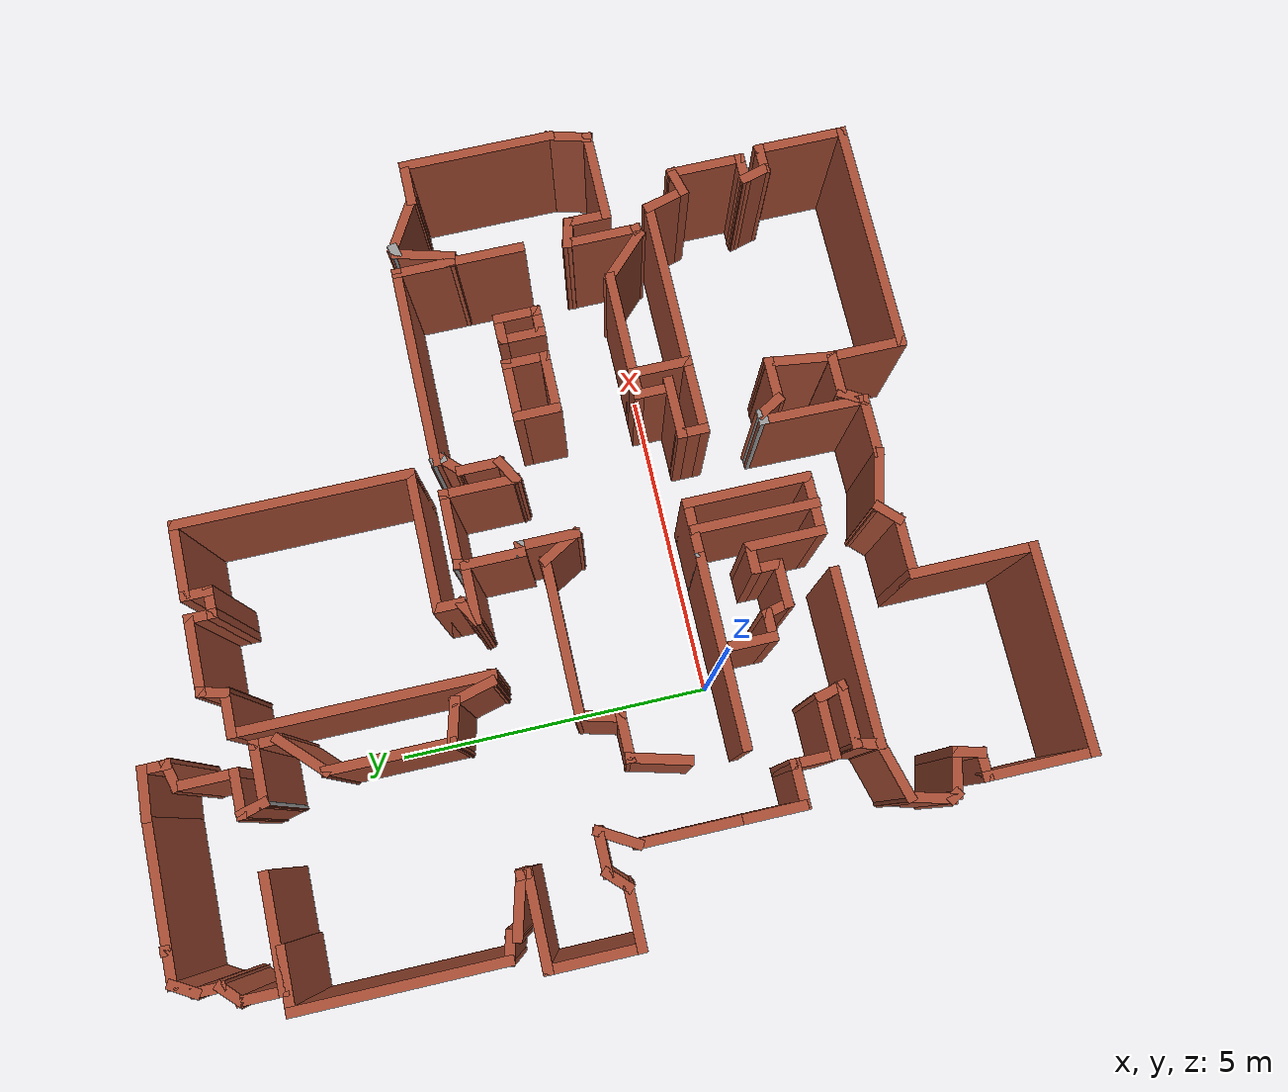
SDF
<?xml version='1.0'?>
<sdf version='1.6'>
  <model name='map_14'>
    <pose frame=''>2.67162 1.68417 0 0 -0 0</pose>
    <link name='Wall_1'>
      <collision name='Wall_1_Collision'>
        <geometry>
          <box>
            <size>0.15 0.15 2.5</size>
          </box>
        </geometry>
        <pose frame=''>0 0 1.25 0 -0 0</pose>
      </collision>
      <visual name='Wall_1_Visual'>
        <pose frame=''>0 0 1.25 0 -0 0</pose>
        <geometry>
          <box>
            <size>0.15 0.15 2.5</size>
          </box>
        </geometry>
        <material>
          <script>
            <uri>file://media/materials/scripts/gazebo.material</uri>
            <name>Gazebo/Bricks</name>
          </script>
          <ambient>1 1 1 1</ambient>
        </material>
        <meta>
          <layer>0</layer>
        </meta>
      </visual>
      <pose frame=''>-4.77548 6.74677 0 0 -0 0</pose>
    </link>
    <link name='Wall_10'>
      <collision name='Wall_10_Collision'>
        <geometry>
          <box>
            <size>1.75 0.15 2.5</size>
          </box>
        </geometry>
        <pose frame=''>0 0 1.25 0 -0 0</pose>
      </collision>
      <visual name='Wall_10_Visual'>
        <pose frame=''>0 0 1.25 0 -0 0</pose>
        <geometry>
          <box>
            <size>1.75 0.15 2.5</size>
          </box>
        </geometry>
        <material>
          <script>
            <uri>file://media/materials/scripts/gazebo.material</uri>
            <name>Gazebo/Bricks</name>
          </script>
          <ambient>1 1 1 1</ambient>
        </material>
        <meta>
          <layer>0</layer>
        </meta>
      </visual>
      <pose frame=''>-4.87484 5.22304 0 0 -0 0</pose>
    </link>
    <link name='Wall_101'>
      <collision name='Wall_101_Collision'>
        <geometry>
          <box>
            <size>1.25 0.15 2.5</size>
          </box>
        </geometry>
        <pose frame=''>0 0 1.25 0 -0 0</pose>
      </collision>
      <visual name='Wall_101_Visual'>
        <pose frame=''>0 0 1.25 0 -0 0</pose>
        <geometry>
          <box>
            <size>1.25 0.15 2.5</size>
          </box>
        </geometry>
        <material>
          <script>
            <uri>file://media/materials/scripts/gazebo.material</uri>
            <name>Gazebo/Bricks</name>
          </script>
          <ambient>1 1 1 1</ambient>
        </material>
        <meta>
          <layer>0</layer>
        </meta>
      </visual>
      <pose frame=''>0.272904 1.65524 0 0 -0 3.14159</pose>
    </link>
    <link name='Wall_102'>
      <collision name='Wall_102_Collision'>
        <geometry>
          <box>
            <size>0.25 0.15 2.5</size>
          </box>
        </geometry>
        <pose frame=''>0 0 1.25 0 -0 0</pose>
      </collision>
      <visual name='Wall_102_Visual'>
        <pose frame=''>0 0 1.25 0 -0 0</pose>
        <geometry>
          <box>
            <size>0.25 0.15 2.5</size>
          </box>
        </geometry>
        <material>
          <script>
            <uri>file://media/materials/scripts/gazebo.material</uri>
            <name>Gazebo/Bricks</name>
          </script>
          <ambient>1 1 1 1</ambient>
        </material>
        <meta>
          <layer>0</layer>
        </meta>
      </visual>
      <pose frame=''>-0.290037 1.60695 0 0 -0 -1.8326</pose>
    </link>
    <link name='Wall_103'>
      <collision name='Wall_103_Collision'>
        <geometry>
          <box>
            <size>1 0.15 2.5</size>
          </box>
        </geometry>
        <pose frame=''>0 0 1.25 0 -0 0</pose>
      </collision>
      <visual name='Wall_103_Visual'>
        <pose frame=''>0 0 1.25 0 -0 0</pose>
        <geometry>
          <box>
            <size>1 0.15 2.5</size>
          </box>
        </geometry>
        <material>
          <script>
            <uri>file://media/materials/scripts/gazebo.material</uri>
            <name>Gazebo/Bricks</name>
          </script>
          <ambient>1 1 1 1</ambient>
        </material>
        <meta>
          <layer>0</layer>
        </meta>
      </visual>
      <pose frame=''>-0.727978 1.55865 0 0 -0 3.14159</pose>
    </link>
    <link name='Wall_104'>
      <collision name='Wall_104_Collision'>
        <geometry>
          <box>
            <size>0.5 0.15 2.5</size>
          </box>
        </geometry>
        <pose frame=''>0 0 1.25 0 -0 0</pose>
      </collision>
      <visual name='Wall_104_Visual'>
        <pose frame=''>0 0 1.25 0 -0 0</pose>
        <geometry>
          <box>
            <size>0.5 0.15 2.5</size>
          </box>
        </geometry>
        <material>
          <script>
            <uri>file://media/materials/scripts/gazebo.material</uri>
            <name>Gazebo/Bricks</name>
          </script>
          <ambient>1 1 1 1</ambient>
        </material>
        <meta>
          <layer>0</layer>
        </meta>
      </visual>
      <pose frame=''>-1.00142 1.64615 0 0 -0 0.523599</pose>
    </link>
    <link name='Wall_105'>
      <collision name='Wall_105_Collision'>
        <geometry>
          <box>
            <size>0.5 0.15 2.5</size>
          </box>
        </geometry>
        <pose frame=''>0 0 1.25 0 -0 0</pose>
      </collision>
      <visual name='Wall_105_Visual'>
        <pose frame=''>0 0 1.25 0 -0 0</pose>
        <geometry>
          <box>
            <size>0.5 0.15 2.5</size>
          </box>
        </geometry>
        <material>
          <script>
            <uri>file://media/materials/scripts/gazebo.material</uri>
            <name>Gazebo/Bricks</name>
          </script>
          <ambient>1 1 1 1</ambient>
        </material>
        <meta>
          <layer>0</layer>
        </meta>
      </visual>
      <pose frame=''>-0.849869 1.90865 0 0 -0 1.5708</pose>
    </link>
    <link name='Wall_106'>
      <collision name='Wall_106_Collision'>
        <geometry>
          <box>
            <size>2.25 0.15 2.5</size>
          </box>
        </geometry>
        <pose frame=''>0 0 1.25 0 -0 0</pose>
      </collision>
      <visual name='Wall_106_Visual'>
        <pose frame=''>0 0 1.25 0 -0 0</pose>
        <geometry>
          <box>
            <size>2.25 0.15 2.5</size>
          </box>
        </geometry>
        <material>
          <script>
            <uri>file://media/materials/scripts/gazebo.material</uri>
            <name>Gazebo/Bricks</name>
          </script>
          <ambient>1 1 1 1</ambient>
        </material>
        <meta>
          <layer>0</layer>
        </meta>
      </visual>
      <pose frame=''>0.200131 2.08365 0 0 -0 0</pose>
    </link>
    <link name='Wall_107'>
      <collision name='Wall_107_Collision'>
        <geometry>
          <box>
            <size>3.75 0.15 2.5</size>
          </box>
        </geometry>
        <pose frame=''>0 0 1.25 0 -0 0</pose>
      </collision>
      <visual name='Wall_107_Visual'>
        <pose frame=''>0 0 1.25 0 -0 0</pose>
        <geometry>
          <box>
            <size>3.75 0.15 2.5</size>
          </box>
        </geometry>
        <material>
          <script>
            <uri>file://media/materials/scripts/gazebo.material</uri>
            <name>Gazebo/Bricks</name>
          </script>
          <ambient>1 1 1 1</ambient>
        </material>
        <meta>
          <layer>0</layer>
        </meta>
      </visual>
      <pose frame=''>1.25013 3.88365 0 0 -0 1.5708</pose>
    </link>
    <link name='Wall_108'>
      <collision name='Wall_108_Collision'>
        <geometry>
          <box>
            <size>1.25 0.15 2.5</size>
          </box>
        </geometry>
        <pose frame=''>0 0 1.25 0 -0 0</pose>
      </collision>
      <visual name='Wall_108_Visual'>
        <pose frame=''>0 0 1.25 0 -0 0</pose>
        <geometry>
          <box>
            <size>1.25 0.15 2.5</size>
          </box>
        </geometry>
        <material>
          <script>
            <uri>file://media/materials/scripts/gazebo.material</uri>
            <name>Gazebo/Bricks</name>
          </script>
          <ambient>1 1 1 1</ambient>
        </material>
        <meta>
          <layer>0</layer>
        </meta>
      </visual>
      <pose frame=''>0.700131 5.68365 0 0 -0 3.14159</pose>
    </link>
    <link name='Wall_109'>
      <collision name='Wall_109_Collision'>
        <geometry>
          <box>
            <size>0.5 0.15 2.5</size>
          </box>
        </geometry>
        <pose frame=''>0 0 1.25 0 -0 0</pose>
      </collision>
      <visual name='Wall_109_Visual'>
        <pose frame=''>0 0 1.25 0 -0 0</pose>
        <geometry>
          <box>
            <size>0.5 0.15 2.5</size>
          </box>
        </geometry>
        <material>
          <script>
            <uri>file://media/materials/scripts/gazebo.material</uri>
            <name>Gazebo/Bricks</name>
          </script>
          <ambient>1 1 1 1</ambient>
        </material>
        <meta>
          <layer>0</layer>
        </meta>
      </visual>
      <pose frame=''>0.150131 5.50865 0 0 -0 -1.5708</pose>
    </link>
    <link name='Wall_110'>
      <collision name='Wall_110_Collision'>
        <geometry>
          <box>
            <size>0.5 0.15 2.5</size>
          </box>
        </geometry>
        <pose frame=''>0 0 1.25 0 -0 0</pose>
      </collision>
      <visual name='Wall_110_Visual'>
        <pose frame=''>0 0 1.25 0 -0 0</pose>
        <geometry>
          <box>
            <size>0.5 0.15 2.5</size>
          </box>
        </geometry>
        <material>
          <script>
            <uri>file://media/materials/scripts/gazebo.material</uri>
            <name>Gazebo/Bricks</name>
          </script>
          <ambient>1 1 1 1</ambient>
        </material>
        <meta>
          <layer>0</layer>
        </meta>
      </visual>
      <pose frame=''>-0.024869 5.33365 0 0 -0 3.14159</pose>
    </link>
    <link name='Wall_111'>
      <collision name='Wall_111_Collision'>
        <geometry>
          <box>
            <size>0.5 0.15 2.5</size>
          </box>
        </geometry>
        <pose frame=''>0 0 1.25 0 -0 0</pose>
      </collision>
      <visual name='Wall_111_Visual'>
        <pose frame=''>0 0 1.25 0 -0 0</pose>
        <geometry>
          <box>
            <size>0.5 0.15 2.5</size>
          </box>
        </geometry>
        <material>
          <script>
            <uri>file://media/materials/scripts/gazebo.material</uri>
            <name>Gazebo/Bricks</name>
          </script>
          <ambient>1 1 1 1</ambient>
        </material>
        <meta>
          <layer>0</layer>
        </meta>
      </visual>
      <pose frame=''>-0.199869 5.50865 0 0 -0 1.5708</pose>
    </link>
    <link name='Wall_112'>
      <collision name='Wall_112_Collision'>
        <geometry>
          <box>
            <size>1.25 0.15 2.5</size>
          </box>
        </geometry>
        <pose frame=''>0 0 1.25 0 -0 0</pose>
      </collision>
      <visual name='Wall_112_Visual'>
        <pose frame=''>0 0 1.25 0 -0 0</pose>
        <geometry>
          <box>
            <size>1.25 0.15 2.5</size>
          </box>
        </geometry>
        <material>
          <script>
            <uri>file://media/materials/scripts/gazebo.material</uri>
            <name>Gazebo/Bricks</name>
          </script>
          <ambient>1 1 1 1</ambient>
        </material>
        <meta>
          <layer>0</layer>
        </meta>
      </visual>
      <pose frame=''>-0.749869 5.68365 0 0 -0 3.14159</pose>
    </link>
    <link name='Wall_113'>
      <collision name='Wall_113_Collision'>
        <geometry>
          <box>
            <size>0.5 0.15 2.5</size>
          </box>
        </geometry>
        <pose frame=''>0 0 1.25 0 -0 0</pose>
      </collision>
      <visual name='Wall_113_Visual'>
        <pose frame=''>0 0 1.25 0 -0 0</pose>
        <geometry>
          <box>
            <size>0.5 0.15 2.5</size>
          </box>
        </geometry>
        <material>
          <script>
            <uri>file://media/materials/scripts/gazebo.material</uri>
            <name>Gazebo/Bricks</name>
          </script>
          <ambient>1 1 1 1</ambient>
        </material>
        <meta>
          <layer>0</layer>
        </meta>
      </visual>
      <pose frame=''>-1.34516 5.51461 0 0 -0 -1.8326</pose>
    </link>
    <link name='Wall_114'>
      <collision name='Wall_114_Collision'>
        <geometry>
          <box>
            <size>0.75 0.15 2.5</size>
          </box>
        </geometry>
        <pose frame=''>0 0 1.25 0 -0 0</pose>
      </collision>
      <visual name='Wall_114_Visual'>
        <pose frame=''>0 0 1.25 0 -0 0</pose>
        <geometry>
          <box>
            <size>0.75 0.15 2.5</size>
          </box>
        </geometry>
        <material>
          <script>
            <uri>file://media/materials/scripts/gazebo.material</uri>
            <name>Gazebo/Bricks</name>
          </script>
          <ambient>1 1 1 1</ambient>
        </material>
        <meta>
          <layer>0</layer>
        </meta>
      </visual>
      <pose frame=''>-1.69046 5.34558 0 0 -0 3.14159</pose>
    </link>
    <link name='Wall_115'>
      <collision name='Wall_115_Collision'>
        <geometry>
          <box>
            <size>4 0.15 2.5</size>
          </box>
        </geometry>
        <pose frame=''>0 0 1.25 0 -0 0</pose>
      </collision>
      <visual name='Wall_115_Visual'>
        <pose frame=''>0 0 1.25 0 -0 0</pose>
        <geometry>
          <box>
            <size>4 0.15 2.5</size>
          </box>
        </geometry>
        <material>
          <script>
            <uri>file://media/materials/scripts/gazebo.material</uri>
            <name>Gazebo/Bricks</name>
          </script>
          <ambient>1 1 1 1</ambient>
        </material>
        <meta>
          <layer>0</layer>
        </meta>
      </visual>
      <pose frame=''>-1.99046 3.42058 0 0 -0 -1.5708</pose>
    </link>
    <link name='Wall_116'>
      <collision name='Wall_116_Collision'>
        <geometry>
          <box>
            <size>0.25 0.15 2.5</size>
          </box>
        </geometry>
        <pose frame=''>0 0 1.25 0 -0 0</pose>
      </collision>
      <visual name='Wall_116_Visual'>
        <pose frame=''>0 0 1.25 0 -0 0</pose>
        <geometry>
          <box>
            <size>0.25 0.15 2.5</size>
          </box>
        </geometry>
        <material>
          <script>
            <uri>file://media/materials/scripts/gazebo.material</uri>
            <name>Gazebo/Bricks</name>
          </script>
          <ambient>1 1 1 1</ambient>
        </material>
        <meta>
          <layer>0</layer>
        </meta>
      </visual>
      <pose frame=''>-2.03875 1.50852 0 0 -0 2.87979</pose>
    </link>
    <link name='Wall_117'>
      <collision name='Wall_117_Collision'>
        <geometry>
          <box>
            <size>0.75 0.15 2.5</size>
          </box>
        </geometry>
        <pose frame=''>0 0 1.25 0 -0 0</pose>
      </collision>
      <visual name='Wall_117_Visual'>
        <pose frame=''>0 0 1.25 0 -0 0</pose>
        <geometry>
          <box>
            <size>0.75 0.15 2.5</size>
          </box>
        </geometry>
        <material>
          <script>
            <uri>file://media/materials/scripts/gazebo.material</uri>
            <name>Gazebo/Bricks</name>
          </script>
          <ambient>1 1 1 1</ambient>
        </material>
        <meta>
          <layer>0</layer>
        </meta>
      </visual>
      <pose frame=''>-2.16469 1.81124 0 0 -0 1.8326</pose>
    </link>
    <link name='Wall_118'>
      <collision name='Wall_118_Collision'>
        <geometry>
          <box>
            <size>0.75 0.15 2.5</size>
          </box>
        </geometry>
        <pose frame=''>0 0 1.25 0 -0 0</pose>
      </collision>
      <visual name='Wall_118_Visual'>
        <pose frame=''>0 0 1.25 0 -0 0</pose>
        <geometry>
          <box>
            <size>0.75 0.15 2.5</size>
          </box>
        </geometry>
        <material>
          <script>
            <uri>file://media/materials/scripts/gazebo.material</uri>
            <name>Gazebo/Bricks</name>
          </script>
          <ambient>1 1 1 1</ambient>
        </material>
        <meta>
          <layer>0</layer>
        </meta>
      </visual>
      <pose frame=''>-2.53212 2.17866 0 0 -0 2.87979</pose>
    </link>
    <link name='Wall_119'>
      <collision name='Wall_119_Collision'>
        <geometry>
          <box>
            <size>2 0.15 2.5</size>
          </box>
        </geometry>
        <pose frame=''>0 0 1.25 0 -0 0</pose>
      </collision>
      <visual name='Wall_119_Visual'>
        <pose frame=''>0 0 1.25 0 -0 0</pose>
        <geometry>
          <box>
            <size>2 0.15 2.5</size>
          </box>
        </geometry>
        <material>
          <script>
            <uri>file://media/materials/scripts/gazebo.material</uri>
            <name>Gazebo/Bricks</name>
          </script>
          <ambient>1 1 1 1</ambient>
        </material>
        <meta>
          <layer>0</layer>
        </meta>
      </visual>
      <pose frame=''>-2.8219 3.18131 0 0 -0 1.5708</pose>
    </link>
    <link name='Wall_12'>
      <collision name='Wall_12_Collision'>
        <geometry>
          <box>
            <size>1 0.15 2.5</size>
          </box>
        </geometry>
        <pose frame=''>0 0 1.25 0 -0 0</pose>
      </collision>
      <visual name='Wall_12_Visual'>
        <pose frame=''>0 0 1.25 0 -0 0</pose>
        <geometry>
          <box>
            <size>1 0.15 2.5</size>
          </box>
        </geometry>
        <material>
          <script>
            <uri>file://media/materials/scripts/gazebo.material</uri>
            <name>Gazebo/Bricks</name>
          </script>
          <ambient>1 1 1 1</ambient>
        </material>
        <meta>
          <layer>0</layer>
        </meta>
      </visual>
      <pose frame=''>-5.54789 5.17389 0 0 -0 3.14159</pose>
    </link>
    <link name='Wall_120'>
      <collision name='Wall_120_Collision'>
        <geometry>
          <box>
            <size>1 0.15 2.5</size>
          </box>
        </geometry>
        <pose frame=''>0 0 1.25 0 -0 0</pose>
      </collision>
      <visual name='Wall_120_Visual'>
        <pose frame=''>0 0 1.25 0 -0 0</pose>
        <geometry>
          <box>
            <size>1 0.15 2.5</size>
          </box>
        </geometry>
        <material>
          <script>
            <uri>file://media/materials/scripts/gazebo.material</uri>
            <name>Gazebo/Bricks</name>
          </script>
          <ambient>1 1 1 1</ambient>
        </material>
        <meta>
          <layer>0</layer>
        </meta>
      </visual>
      <pose frame=''>-2.52137 4.40683 0 0 -0 0.785398</pose>
    </link>
    <link name='Wall_121'>
      <collision name='Wall_121_Collision'>
        <geometry>
          <box>
            <size>0.5 0.15 2.5</size>
          </box>
        </geometry>
        <pose frame=''>0 0 1.25 0 -0 0</pose>
      </collision>
      <visual name='Wall_121_Visual'>
        <pose frame=''>0 0 1.25 0 -0 0</pose>
        <geometry>
          <box>
            <size>0.5 0.15 2.5</size>
          </box>
        </geometry>
        <material>
          <script>
            <uri>file://media/materials/scripts/gazebo.material</uri>
            <name>Gazebo/Bricks</name>
          </script>
          <ambient>1 1 1 1</ambient>
        </material>
        <meta>
          <layer>0</layer>
        </meta>
      </visual>
      <pose frame=''>-2.22085 4.88235 0 0 -0 1.5708</pose>
    </link>
    <link name='Wall_123'>
      <collision name='Wall_123_Collision'>
        <geometry>
          <box>
            <size>0.25 0.15 2.5</size>
          </box>
        </geometry>
        <pose frame=''>0 0 1.25 0 -0 0</pose>
      </collision>
      <visual name='Wall_123_Visual'>
        <pose frame=''>0 0 1.25 0 -0 0</pose>
        <geometry>
          <box>
            <size>0.25 0.15 2.5</size>
          </box>
        </geometry>
        <material>
          <script>
            <uri>file://media/materials/scripts/gazebo.material</uri>
            <name>Gazebo/Grey</name>
          </script>
          <ambient>1 1 1 1</ambient>
        </material>
        <meta>
          <layer>0</layer>
        </meta>
      </visual>
      <pose frame=''>-3.08379 5.10564 0 0 -0 1.8326</pose>
    </link>
    <link name='Wall_126'>
      <collision name='Wall_126_Collision'>
        <geometry>
          <box>
            <size>0.25 0.15 2.5</size>
          </box>
        </geometry>
        <pose frame=''>0 0 1.25 0 -0 0</pose>
      </collision>
      <visual name='Wall_126_Visual'>
        <pose frame=''>0 0 1.25 0 -0 0</pose>
        <geometry>
          <box>
            <size>0.25 0.15 2.5</size>
          </box>
        </geometry>
        <material>
          <script>
            <uri>file://media/materials/scripts/gazebo.material</uri>
            <name>Gazebo/Grey</name>
          </script>
          <ambient>1 1 1 1</ambient>
        </material>
        <meta>
          <layer>0</layer>
        </meta>
      </visual>
      <pose frame=''>-3.08379 5.10564 0 0 -0 1.8326</pose>
    </link>
    <link name='Wall_129'>
      <collision name='Wall_129_Collision'>
        <geometry>
          <box>
            <size>1 0.15 2.5</size>
          </box>
        </geometry>
        <pose frame=''>0 0 1.25 0 -0 0</pose>
      </collision>
      <visual name='Wall_129_Visual'>
        <pose frame=''>0 0 1.25 0 -0 0</pose>
        <geometry>
          <box>
            <size>1 0.15 2.5</size>
          </box>
        </geometry>
        <material>
          <script>
            <uri>file://media/materials/scripts/gazebo.material</uri>
            <name>Gazebo/Bricks</name>
          </script>
          <ambient>1 1 1 1</ambient>
        </material>
        <meta>
          <layer>0</layer>
        </meta>
      </visual>
      <pose frame=''>-2.64585 5.05735 0 0 -0 3.14159</pose>
    </link>
    <link name='Wall_13'>
      <collision name='Wall_13_Collision'>
        <geometry>
          <box>
            <size>3.25 0.15 2.5</size>
          </box>
        </geometry>
        <pose frame=''>0 0 1.25 0 -0 0</pose>
      </collision>
      <visual name='Wall_13_Visual'>
        <pose frame=''>0 0 1.25 0 -0 0</pose>
        <geometry>
          <box>
            <size>3.25 0.15 2.5</size>
          </box>
        </geometry>
        <material>
          <script>
            <uri>file://media/materials/scripts/gazebo.material</uri>
            <name>Gazebo/Bricks</name>
          </script>
          <ambient>1 1 1 1</ambient>
        </material>
        <meta>
          <layer>0</layer>
        </meta>
      </visual>
      <pose frame=''>-5.97289 3.62389 0 0 -0 -1.5708</pose>
    </link>
    <link name='Wall_130'>
      <collision name='Wall_130_Collision'>
        <geometry>
          <box>
            <size>0.5 0.15 2.5</size>
          </box>
        </geometry>
        <pose frame=''>0 0 1.25 0 -0 0</pose>
      </collision>
      <visual name='Wall_130_Visual'>
        <pose frame=''>0 0 1.25 0 -0 0</pose>
        <geometry>
          <box>
            <size>0.5 0.15 2.5</size>
          </box>
        </geometry>
        <material>
          <script>
            <uri>file://media/materials/scripts/gazebo.material</uri>
            <name>Gazebo/Bricks</name>
          </script>
          <ambient>1 1 1 1</ambient>
        </material>
        <meta>
          <layer>0</layer>
        </meta>
      </visual>
      <pose frame=''>-3.11615 5.22638 0 0 -0 1.8326</pose>
    </link>
    <link name='Wall_133'>
      <collision name='Wall_133_Collision'>
        <geometry>
          <box>
            <size>0.75 0.15 2.5</size>
          </box>
        </geometry>
        <pose frame=''>0 0 1.25 0 -0 0</pose>
      </collision>
      <visual name='Wall_133_Visual'>
        <pose frame=''>0 0 1.25 0 -0 0</pose>
        <geometry>
          <box>
            <size>0.75 0.15 2.5</size>
          </box>
        </geometry>
        <material>
          <script>
            <uri>file://media/materials/scripts/gazebo.material</uri>
            <name>Gazebo/Bricks</name>
          </script>
          <ambient>1 1 1 1</ambient>
        </material>
        <meta>
          <layer>0</layer>
        </meta>
      </visual>
      <pose frame=''>-2.86144 5.39542 0 0 -0 0</pose>
    </link>
    <link name='Wall_134'>
      <collision name='Wall_134_Collision'>
        <geometry>
          <box>
            <size>1 0.15 2.5</size>
          </box>
        </geometry>
        <pose frame=''>0 0 1.25 0 -0 0</pose>
      </collision>
      <visual name='Wall_134_Visual'>
        <pose frame=''>0 0 1.25 0 -0 0</pose>
        <geometry>
          <box>
            <size>1 0.15 2.5</size>
          </box>
        </geometry>
        <material>
          <script>
            <uri>file://media/materials/scripts/gazebo.material</uri>
            <name>Gazebo/Bricks</name>
          </script>
          <ambient>1 1 1 1</ambient>
        </material>
        <meta>
          <layer>0</layer>
        </meta>
      </visual>
      <pose frame=''>-2.56144 5.82042 0 0 -0 1.5708</pose>
    </link>
    <link name='Wall_135'>
      <collision name='Wall_135_Collision'>
        <geometry>
          <box>
            <size>0.5 0.15 2.5</size>
          </box>
        </geometry>
        <pose frame=''>0 0 1.25 0 -0 0</pose>
      </collision>
      <visual name='Wall_135_Visual'>
        <pose frame=''>0 0 1.25 0 -0 0</pose>
        <geometry>
          <box>
            <size>0.5 0.15 2.5</size>
          </box>
        </geometry>
        <material>
          <script>
            <uri>file://media/materials/scripts/gazebo.material</uri>
            <name>Gazebo/Bricks</name>
          </script>
          <ambient>1 1 1 1</ambient>
        </material>
        <meta>
          <layer>0</layer>
        </meta>
      </visual>
      <pose frame=''>-2.3924 6.29071 0 0 -0 0.261799</pose>
    </link>
    <link name='Wall_136'>
      <collision name='Wall_136_Collision'>
        <geometry>
          <box>
            <size>0.5 0.15 2.5</size>
          </box>
        </geometry>
        <pose frame=''>0 0 1.25 0 -0 0</pose>
      </collision>
      <visual name='Wall_136_Visual'>
        <pose frame=''>0 0 1.25 0 -0 0</pose>
        <geometry>
          <box>
            <size>0.5 0.15 2.5</size>
          </box>
        </geometry>
        <material>
          <script>
            <uri>file://media/materials/scripts/gazebo.material</uri>
            <name>Gazebo/Bricks</name>
          </script>
          <ambient>1 1 1 1</ambient>
        </material>
        <meta>
          <layer>0</layer>
        </meta>
      </visual>
      <pose frame=''>-2.22337 6.51101 0 0 -0 1.5708</pose>
    </link>
    <link name='Wall_137'>
      <collision name='Wall_137_Collision'>
        <geometry>
          <box>
            <size>0.830025 0.15 2.5</size>
          </box>
        </geometry>
        <pose frame=''>0 0 1.25 0 -0 0</pose>
      </collision>
      <visual name='Wall_137_Visual'>
        <pose frame=''>0 0 1.25 0 -0 0</pose>
        <geometry>
          <box>
            <size>0.830025 0.15 2.5</size>
          </box>
        </geometry>
        <material>
          <script>
            <uri>file://media/materials/scripts/gazebo.material</uri>
            <name>Gazebo/Bricks</name>
          </script>
          <ambient>1 1 1 1</ambient>
        </material>
        <meta>
          <layer>0</layer>
        </meta>
      </visual>
      <pose frame=''>-2.56286 6.70482 0 0 -0 3.08623</pose>
    </link>
    <link name='Wall_14'>
      <collision name='Wall_14_Collision'>
        <geometry>
          <box>
            <size>0.5 0.15 2.5</size>
          </box>
        </geometry>
        <pose frame=''>0 0 1.25 0 -0 0</pose>
      </collision>
      <visual name='Wall_14_Visual'>
        <pose frame=''>0 0 1.25 0 -0 0</pose>
        <geometry>
          <box>
            <size>0.5 0.15 2.5</size>
          </box>
        </geometry>
        <material>
          <script>
            <uri>file://media/materials/scripts/gazebo.material</uri>
            <name>Gazebo/Bricks</name>
          </script>
          <ambient>1 1 1 1</ambient>
        </material>
        <meta>
          <layer>0</layer>
        </meta>
      </visual>
      <pose frame=''>-5.80385 2.0286 0 0 -0 -0.261799</pose>
    </link>
    <link name='Wall_140'>
      <collision name='Wall_140_Collision'>
        <geometry>
          <box>
            <size>1.25 0.15 2.5</size>
          </box>
        </geometry>
        <pose frame=''>0 0 1.25 0 -0 0</pose>
      </collision>
      <visual name='Wall_140_Visual'>
        <pose frame=''>0 0 1.25 0 -0 0</pose>
        <geometry>
          <box>
            <size>1.25 0.15 2.5</size>
          </box>
        </geometry>
        <material>
          <script>
            <uri>file://media/materials/scripts/gazebo.material</uri>
            <name>Gazebo/Bricks</name>
          </script>
          <ambient>1 1 1 1</ambient>
        </material>
        <meta>
          <layer>0</layer>
        </meta>
      </visual>
      <pose frame=''>4.44762 0.274324 0 0 -0 -1.5708</pose>
    </link>
    <link name='Wall_142'>
      <collision name='Wall_142_Collision'>
        <geometry>
          <box>
            <size>0.75 0.15 2.5</size>
          </box>
        </geometry>
        <pose frame=''>0 0 1.25 0 -0 0</pose>
      </collision>
      <visual name='Wall_142_Visual'>
        <pose frame=''>0 0 1.25 0 -0 0</pose>
        <geometry>
          <box>
            <size>0.75 0.15 2.5</size>
          </box>
        </geometry>
        <material>
          <script>
            <uri>file://media/materials/scripts/gazebo.material</uri>
            <name>Gazebo/Bricks</name>
          </script>
          <ambient>1 1 1 1</ambient>
        </material>
        <meta>
          <layer>0</layer>
        </meta>
      </visual>
      <pose frame=''>1.77003 0.016461 0 0 -0 -1.5708</pose>
    </link>
    <link name='Wall_143'>
      <collision name='Wall_143_Collision'>
        <geometry>
          <box>
            <size>1 0.15 2.5</size>
          </box>
        </geometry>
        <pose frame=''>0 0 1.25 0 -0 0</pose>
      </collision>
      <visual name='Wall_143_Visual'>
        <pose frame=''>0 0 1.25 0 -0 0</pose>
        <geometry>
          <box>
            <size>1 0.15 2.5</size>
          </box>
        </geometry>
        <material>
          <script>
            <uri>file://media/materials/scripts/gazebo.material</uri>
            <name>Gazebo/Bricks</name>
          </script>
          <ambient>1 1 1 1</ambient>
        </material>
        <meta>
          <layer>0</layer>
        </meta>
      </visual>
      <pose frame=''>2.19503 -0.283539 0 0 -0 0</pose>
    </link>
    <link name='Wall_144'>
      <collision name='Wall_144_Collision'>
        <geometry>
          <box>
            <size>0.75 0.15 2.5</size>
          </box>
        </geometry>
        <pose frame=''>0 0 1.25 0 -0 0</pose>
      </collision>
      <visual name='Wall_144_Visual'>
        <pose frame=''>0 0 1.25 0 -0 0</pose>
        <geometry>
          <box>
            <size>0.75 0.15 2.5</size>
          </box>
        </geometry>
        <material>
          <script>
            <uri>file://media/materials/scripts/gazebo.material</uri>
            <name>Gazebo/Bricks</name>
          </script>
          <ambient>1 1 1 1</ambient>
        </material>
        <meta>
          <layer>0</layer>
        </meta>
      </visual>
      <pose frame=''>2.62003 0.016461 0 0 -0 1.5708</pose>
    </link>
    <link name='Wall_145'>
      <collision name='Wall_145_Collision'>
        <geometry>
          <box>
            <size>1 0.15 2.5</size>
          </box>
        </geometry>
        <pose frame=''>0 0 1.25 0 -0 0</pose>
      </collision>
      <visual name='Wall_145_Visual'>
        <pose frame=''>0 0 1.25 0 -0 0</pose>
        <geometry>
          <box>
            <size>1 0.15 2.5</size>
          </box>
        </geometry>
        <material>
          <script>
            <uri>file://media/materials/scripts/gazebo.material</uri>
            <name>Gazebo/Bricks</name>
          </script>
          <ambient>1 1 1 1</ambient>
        </material>
        <meta>
          <layer>0</layer>
        </meta>
      </visual>
      <pose frame=''>2.19503 0.316462 0 0 -0 3.14159</pose>
    </link>
    <link name='Wall_148'>
      <collision name='Wall_148_Collision'>
        <geometry>
          <box>
            <size>0.75 0.15 2.5</size>
          </box>
        </geometry>
        <pose frame=''>0 0 1.25 0 -0 0</pose>
      </collision>
      <visual name='Wall_148_Visual'>
        <pose frame=''>0 0 1.25 0 -0 0</pose>
        <geometry>
          <box>
            <size>0.75 0.15 2.5</size>
          </box>
        </geometry>
        <material>
          <script>
            <uri>file://media/materials/scripts/gazebo.material</uri>
            <name>Gazebo/Bricks</name>
          </script>
          <ambient>1 1 1 1</ambient>
        </material>
        <meta>
          <layer>0</layer>
        </meta>
      </visual>
      <pose frame=''>3.02129 -0.004847 0 0 -0 -1.5708</pose>
    </link>
    <link name='Wall_149'>
      <collision name='Wall_149_Collision'>
        <geometry>
          <box>
            <size>0.5 0.15 2.5</size>
          </box>
        </geometry>
        <pose frame=''>0 0 1.25 0 -0 0</pose>
      </collision>
      <visual name='Wall_149_Visual'>
        <pose frame=''>0 0 1.25 0 -0 0</pose>
        <geometry>
          <box>
            <size>0.5 0.15 2.5</size>
          </box>
        </geometry>
        <material>
          <script>
            <uri>file://media/materials/scripts/gazebo.material</uri>
            <name>Gazebo/Bricks</name>
          </script>
          <ambient>1 1 1 1</ambient>
        </material>
        <meta>
          <layer>0</layer>
        </meta>
      </visual>
      <pose frame=''>3.19629 -0.304847 0 0 -0 0</pose>
    </link>
    <link name='Wall_15'>
      <collision name='Wall_15_Collision'>
        <geometry>
          <box>
            <size>0.25 0.15 2.5</size>
          </box>
        </geometry>
        <pose frame=''>0 0 1.25 0 -0 0</pose>
      </collision>
      <visual name='Wall_15_Visual'>
        <pose frame=''>0 0 1.25 0 -0 0</pose>
        <geometry>
          <box>
            <size>0.25 0.15 2.5</size>
          </box>
        </geometry>
        <material>
          <script>
            <uri>file://media/materials/scripts/gazebo.material</uri>
            <name>Gazebo/Bricks</name>
          </script>
          <ambient>1 1 1 1</ambient>
        </material>
        <meta>
          <layer>0</layer>
        </meta>
      </visual>
      <pose frame=''>-5.65981 1.94 0 0 -0 -2.0944</pose>
    </link>
    <link name='Wall_150'>
      <collision name='Wall_150_Collision'>
        <geometry>
          <box>
            <size>0.75 0.15 2.5</size>
          </box>
        </geometry>
        <pose frame=''>0 0 1.25 0 -0 0</pose>
      </collision>
      <visual name='Wall_150_Visual'>
        <pose frame=''>0 0 1.25 0 -0 0</pose>
        <geometry>
          <box>
            <size>0.75 0.15 2.5</size>
          </box>
        </geometry>
        <material>
          <script>
            <uri>file://media/materials/scripts/gazebo.material</uri>
            <name>Gazebo/Bricks</name>
          </script>
          <ambient>1 1 1 1</ambient>
        </material>
        <meta>
          <layer>0</layer>
        </meta>
      </visual>
      <pose frame=''>3.37129 -0.004847 0 0 -0 1.5708</pose>
    </link>
    <link name='Wall_151'>
      <collision name='Wall_151_Collision'>
        <geometry>
          <box>
            <size>0.5 0.15 2.5</size>
          </box>
        </geometry>
        <pose frame=''>0 0 1.25 0 -0 0</pose>
      </collision>
      <visual name='Wall_151_Visual'>
        <pose frame=''>0 0 1.25 0 -0 0</pose>
        <geometry>
          <box>
            <size>0.5 0.15 2.5</size>
          </box>
        </geometry>
        <material>
          <script>
            <uri>file://media/materials/scripts/gazebo.material</uri>
            <name>Gazebo/Bricks</name>
          </script>
          <ambient>1 1 1 1</ambient>
        </material>
        <meta>
          <layer>0</layer>
        </meta>
      </visual>
      <pose frame=''>3.19629 0.295153 0 0 -0 3.14159</pose>
    </link>
    <link name='Wall_153'>
      <collision name='Wall_153_Collision'>
        <geometry>
          <box>
            <size>1 0.15 2.5</size>
          </box>
        </geometry>
        <pose frame=''>0 0 1.25 0 -0 0</pose>
      </collision>
      <visual name='Wall_153_Visual'>
        <pose frame=''>0 0 1.25 0 -0 0</pose>
        <geometry>
          <box>
            <size>1 0.15 2.5</size>
          </box>
        </geometry>
        <material>
          <script>
            <uri>file://media/materials/scripts/gazebo.material</uri>
            <name>Gazebo/Bricks</name>
          </script>
          <ambient>1 1 1 1</ambient>
        </material>
        <meta>
          <layer>0</layer>
        </meta>
      </visual>
      <pose frame=''>-0.302978 1.13365 0 0 -0 -1.5708</pose>
    </link>
    <link name='Wall_154'>
      <collision name='Wall_154_Collision'>
        <geometry>
          <box>
            <size>0.25 0.15 2.5</size>
          </box>
        </geometry>
        <pose frame=''>0 0 1.25 0 -0 0</pose>
      </collision>
      <visual name='Wall_154_Visual'>
        <pose frame=''>0 0 1.25 0 -0 0</pose>
        <geometry>
          <box>
            <size>0.25 0.15 2.5</size>
          </box>
        </geometry>
        <material>
          <script>
            <uri>file://media/materials/scripts/gazebo.material</uri>
            <name>Gazebo/Grey</name>
          </script>
          <ambient>1 1 1 1</ambient>
        </material>
        <meta>
          <layer>0</layer>
        </meta>
      </visual>
      <pose frame=''>-0.252978 0.708652 0 0 -0 0</pose>
    </link>
    <link name='Wall_155'>
      <collision name='Wall_155_Collision'>
        <geometry>
          <box>
            <size>1 0.15 2.5</size>
          </box>
        </geometry>
        <pose frame=''>0 0 1.25 0 -0 0</pose>
      </collision>
      <visual name='Wall_155_Visual'>
        <pose frame=''>0 0 1.25 0 -0 0</pose>
        <geometry>
          <box>
            <size>1 0.15 2.5</size>
          </box>
        </geometry>
        <material>
          <script>
            <uri>file://media/materials/scripts/gazebo.material</uri>
            <name>Gazebo/Bricks</name>
          </script>
          <ambient>1 1 1 1</ambient>
        </material>
        <meta>
          <layer>0</layer>
        </meta>
      </visual>
      <pose frame=''>-0.202978 0.283651 0 0 -0 -1.5708</pose>
    </link>
    <link name='Wall_156'>
      <collision name='Wall_156_Collision'>
        <geometry>
          <box>
            <size>0.15 0.15 2.5</size>
          </box>
        </geometry>
        <pose frame=''>0 0 1.25 0 -0 0</pose>
      </collision>
      <visual name='Wall_156_Visual'>
        <pose frame=''>0 0 1.25 0 -0 0</pose>
        <geometry>
          <box>
            <size>0.15 0.15 2.5</size>
          </box>
        </geometry>
        <material>
          <script>
            <uri>file://media/materials/scripts/gazebo.material</uri>
            <name>Gazebo/Bricks</name>
          </script>
          <ambient>1 1 1 1</ambient>
        </material>
        <meta>
          <layer>0</layer>
        </meta>
      </visual>
      <pose frame=''>-0.202978 -0.141349 0 0 -0 0</pose>
    </link>
    <link name='Wall_157'>
      <collision name='Wall_157_Collision'>
        <geometry>
          <box>
            <size>0.75 0.15 2.5</size>
          </box>
        </geometry>
        <pose frame=''>0 0 1.25 0 -0 0</pose>
      </collision>
      <visual name='Wall_157_Visual'>
        <pose frame=''>0 0 1.25 0 -0 0</pose>
        <geometry>
          <box>
            <size>0.75 0.15 2.5</size>
          </box>
        </geometry>
        <material>
          <script>
            <uri>file://media/materials/scripts/gazebo.material</uri>
            <name>Gazebo/Bricks</name>
          </script>
          <ambient>1 1 1 1</ambient>
        </material>
        <meta>
          <layer>0</layer>
        </meta>
      </visual>
      <pose frame=''>-0.352978 0.118459 0 0 -0 2.0944</pose>
    </link>
    <link name='Wall_158'>
      <collision name='Wall_158_Collision'>
        <geometry>
          <box>
            <size>2.5 0.15 2.5</size>
          </box>
        </geometry>
        <pose frame=''>0 0 1.25 0 -0 0</pose>
      </collision>
      <visual name='Wall_158_Visual'>
        <pose frame=''>0 0 1.25 0 -0 0</pose>
        <geometry>
          <box>
            <size>2.5 0.15 2.5</size>
          </box>
        </geometry>
        <material>
          <script>
            <uri>file://media/materials/scripts/gazebo.material</uri>
            <name>Gazebo/Bricks</name>
          </script>
          <ambient>1 1 1 1</ambient>
        </material>
        <meta>
          <layer>0</layer>
        </meta>
      </visual>
      <pose frame=''>-1.67798 0.378267 0 0 -0 3.14159</pose>
    </link>
    <link name='Wall_159'>
      <collision name='Wall_159_Collision'>
        <geometry>
          <box>
            <size>0.75 0.15 2.5</size>
          </box>
        </geometry>
        <pose frame=''>0 0 1.25 0 -0 0</pose>
      </collision>
      <visual name='Wall_159_Visual'>
        <pose frame=''>0 0 1.25 0 -0 0</pose>
        <geometry>
          <box>
            <size>0.75 0.15 2.5</size>
          </box>
        </geometry>
        <material>
          <script>
            <uri>file://media/materials/scripts/gazebo.material</uri>
            <name>Gazebo/Bricks</name>
          </script>
          <ambient>1 1 1 1</ambient>
        </material>
        <meta>
          <layer>0</layer>
        </meta>
      </visual>
      <pose frame=''>-2.93062 0.088489 0 0 -0 -1.8326</pose>
    </link>
    <link name='Wall_16'>
      <collision name='Wall_16_Collision'>
        <geometry>
          <box>
            <size>1 0.15 2.5</size>
          </box>
        </geometry>
        <pose frame=''>0 0 1.25 0 -0 0</pose>
      </collision>
      <visual name='Wall_16_Visual'>
        <pose frame=''>0 0 1.25 0 -0 0</pose>
        <geometry>
          <box>
            <size>1 0.15 2.5</size>
          </box>
        </geometry>
        <material>
          <script>
            <uri>file://media/materials/scripts/gazebo.material</uri>
            <name>Gazebo/Bricks</name>
          </script>
          <ambient>1 1 1 1</ambient>
        </material>
        <meta>
          <layer>0</layer>
        </meta>
      </visual>
      <pose frame=''>-5.2743 1.7867 0 0 -0 -0.261799</pose>
    </link>
    <link name='Wall_160'>
      <collision name='Wall_160_Collision'>
        <geometry>
          <box>
            <size>0.75 0.15 2.5</size>
          </box>
        </geometry>
        <pose frame=''>0 0 1.25 0 -0 0</pose>
      </collision>
      <visual name='Wall_160_Visual'>
        <pose frame=''>0 0 1.25 0 -0 0</pose>
        <geometry>
          <box>
            <size>0.75 0.15 2.5</size>
          </box>
        </geometry>
        <material>
          <script>
            <uri>file://media/materials/scripts/gazebo.material</uri>
            <name>Gazebo/Bricks</name>
          </script>
          <ambient>1 1 1 1</ambient>
        </material>
        <meta>
          <layer>0</layer>
        </meta>
      </visual>
      <pose frame=''>-3.30827 -0.201289 0 0 -0 3.14159</pose>
    </link>
    <link name='Wall_161'>
      <collision name='Wall_161_Collision'>
        <geometry>
          <box>
            <size>1 0.15 2.5</size>
          </box>
        </geometry>
        <pose frame=''>0 0 1.25 0 -0 0</pose>
      </collision>
      <visual name='Wall_161_Visual'>
        <pose frame=''>0 0 1.25 0 -0 0</pose>
        <geometry>
          <box>
            <size>1 0.15 2.5</size>
          </box>
        </geometry>
        <material>
          <script>
            <uri>file://media/materials/scripts/gazebo.material</uri>
            <name>Gazebo/Bricks</name>
          </script>
          <ambient>1 1 1 1</ambient>
        </material>
        <meta>
          <layer>0</layer>
        </meta>
      </visual>
      <pose frame=''>-3.71827 -0.611807 0 0 -0 -1.8326</pose>
    </link>
    <link name='Wall_163'>
      <collision name='Wall_163_Collision'>
        <geometry>
          <box>
            <size>3 0.15 2.5</size>
          </box>
        </geometry>
        <pose frame=''>0 0 1.25 0 -0 0</pose>
      </collision>
      <visual name='Wall_163_Visual'>
        <pose frame=''>0 0 1.25 0 -0 0</pose>
        <geometry>
          <box>
            <size>3 0.15 2.5</size>
          </box>
        </geometry>
        <material>
          <script>
            <uri>file://media/materials/scripts/gazebo.material</uri>
            <name>Gazebo/Bricks</name>
          </script>
          <ambient>1 1 1 1</ambient>
        </material>
        <meta>
          <layer>0</layer>
        </meta>
      </visual>
      <pose frame=''>-2.39233 -1.87711 0 0 -0 0</pose>
    </link>
    <link name='Wall_164'>
      <collision name='Wall_164_Collision'>
        <geometry>
          <box>
            <size>0.15 0.15 2.5</size>
          </box>
        </geometry>
        <pose frame=''>0 0 1.25 0 -0 0</pose>
      </collision>
      <visual name='Wall_164_Visual'>
        <pose frame=''>0 0 1.25 0 -0 0</pose>
        <geometry>
          <box>
            <size>0.15 0.15 2.5</size>
          </box>
        </geometry>
        <material>
          <script>
            <uri>file://media/materials/scripts/gazebo.material</uri>
            <name>Gazebo/Grey</name>
          </script>
          <ambient>1 1 1 1</ambient>
        </material>
        <meta>
          <layer>0</layer>
        </meta>
      </visual>
      <pose frame=''>-0.967326 -1.87711 0 0 -0 0</pose>
    </link>
    <link name='Wall_165'>
      <collision name='Wall_165_Collision'>
        <geometry>
          <box>
            <size>1 0.15 2.5</size>
          </box>
        </geometry>
        <pose frame=''>0 0 1.25 0 -0 0</pose>
      </collision>
      <visual name='Wall_165_Visual'>
        <pose frame=''>0 0 1.25 0 -0 0</pose>
        <geometry>
          <box>
            <size>1 0.15 2.5</size>
          </box>
        </geometry>
        <material>
          <script>
            <uri>file://media/materials/scripts/gazebo.material</uri>
            <name>Gazebo/Bricks</name>
          </script>
          <ambient>1 1 1 1</ambient>
        </material>
        <meta>
          <layer>0</layer>
        </meta>
      </visual>
      <pose frame=''>-0.542326 -1.87711 0 0 -0 0</pose>
    </link>
    <link name='Wall_166'>
      <collision name='Wall_166_Collision'>
        <geometry>
          <box>
            <size>2 0.15 2.5</size>
          </box>
        </geometry>
        <pose frame=''>0 0 1.25 0 -0 0</pose>
      </collision>
      <visual name='Wall_166_Visual'>
        <pose frame=''>0 0 1.25 0 -0 0</pose>
        <geometry>
          <box>
            <size>2 0.15 2.5</size>
          </box>
        </geometry>
        <material>
          <script>
            <uri>file://media/materials/scripts/gazebo.material</uri>
            <name>Gazebo/Bricks</name>
          </script>
          <ambient>1 1 1 1</ambient>
        </material>
        <meta>
          <layer>0</layer>
        </meta>
      </visual>
      <pose frame=''>-0.117326 -2.80211 0 0 -0 -1.5708</pose>
    </link>
    <link name='Wall_167'>
      <collision name='Wall_167_Collision'>
        <geometry>
          <box>
            <size>1 0.15 2.5</size>
          </box>
        </geometry>
        <pose frame=''>0 0 1.25 0 -0 0</pose>
      </collision>
      <visual name='Wall_167_Visual'>
        <pose frame=''>0 0 1.25 0 -0 0</pose>
        <geometry>
          <box>
            <size>1 0.15 2.5</size>
          </box>
        </geometry>
        <material>
          <script>
            <uri>file://media/materials/scripts/gazebo.material</uri>
            <name>Gazebo/Bricks</name>
          </script>
          <ambient>1 1 1 1</ambient>
        </material>
        <meta>
          <layer>0</layer>
        </meta>
      </visual>
      <pose frame=''>-0.542326 -3.72711 0 0 -0 3.14159</pose>
    </link>
    <link name='Wall_168'>
      <collision name='Wall_168_Collision'>
        <geometry>
          <box>
            <size>1.25 0.15 2.5</size>
          </box>
        </geometry>
        <pose frame=''>0 0 1.25 0 -0 0</pose>
      </collision>
      <visual name='Wall_168_Visual'>
        <pose frame=''>0 0 1.25 0 -0 0</pose>
        <geometry>
          <box>
            <size>1.25 0.15 2.5</size>
          </box>
        </geometry>
        <material>
          <script>
            <uri>file://media/materials/scripts/gazebo.material</uri>
            <name>Gazebo/Bricks</name>
          </script>
          <ambient>1 1 1 1</ambient>
        </material>
        <meta>
          <layer>0</layer>
        </meta>
      </visual>
      <pose frame=''>-0.967326 -3.17711 0 0 -0 1.5708</pose>
    </link>
    <link name='Wall_169'>
      <collision name='Wall_169_Collision'>
        <geometry>
          <box>
            <size>0.5 0.15 2.5</size>
          </box>
        </geometry>
        <pose frame=''>0 0 1.25 0 -0 0</pose>
      </collision>
      <visual name='Wall_169_Visual'>
        <pose frame=''>0 0 1.25 0 -0 0</pose>
        <geometry>
          <box>
            <size>0.5 0.15 2.5</size>
          </box>
        </geometry>
        <material>
          <script>
            <uri>file://media/materials/scripts/gazebo.material</uri>
            <name>Gazebo/Bricks</name>
          </script>
          <ambient>1 1 1 1</ambient>
        </material>
        <meta>
          <layer>0</layer>
        </meta>
      </visual>
      <pose frame=''>-1.14233 -2.62711 0 0 -0 3.14159</pose>
    </link>
    <link name='Wall_17'>
      <collision name='Wall_17_Collision'>
        <geometry>
          <box>
            <size>0.25 0.15 2.5</size>
          </box>
        </geometry>
        <pose frame=''>0 0 1.25 0 -0 0</pose>
      </collision>
      <visual name='Wall_17_Visual'>
        <pose frame=''>0 0 1.25 0 -0 0</pose>
        <geometry>
          <box>
            <size>0.25 0.15 2.5</size>
          </box>
        </geometry>
        <material>
          <script>
            <uri>file://media/materials/scripts/gazebo.material</uri>
            <name>Gazebo/Bricks</name>
          </script>
          <ambient>1 1 1 1</ambient>
        </material>
        <meta>
          <layer>0</layer>
        </meta>
      </visual>
      <pose frame=''>-4.86378 1.6267 0 0 -0 -1.5708</pose>
    </link>
    <link name='Wall_170'>
      <collision name='Wall_170_Collision'>
        <geometry>
          <box>
            <size>0.5 0.15 2.5</size>
          </box>
        </geometry>
        <pose frame=''>0 0 1.25 0 -0 0</pose>
      </collision>
      <visual name='Wall_170_Visual'>
        <pose frame=''>0 0 1.25 0 -0 0</pose>
        <geometry>
          <box>
            <size>0.5 0.15 2.5</size>
          </box>
        </geometry>
        <material>
          <script>
            <uri>file://media/materials/scripts/gazebo.material</uri>
            <name>Gazebo/Bricks</name>
          </script>
          <ambient>1 1 1 1</ambient>
        </material>
        <meta>
          <layer>0</layer>
        </meta>
      </visual>
      <pose frame=''>-1.31733 -2.80211 0 0 -0 -1.5708</pose>
    </link>
    <link name='Wall_171'>
      <collision name='Wall_171_Collision'>
        <geometry>
          <box>
            <size>0.75 0.15 2.5</size>
          </box>
        </geometry>
        <pose frame=''>0 0 1.25 0 -0 0</pose>
      </collision>
      <visual name='Wall_171_Visual'>
        <pose frame=''>0 0 1.25 0 -0 0</pose>
        <geometry>
          <box>
            <size>0.75 0.15 2.5</size>
          </box>
        </geometry>
        <material>
          <script>
            <uri>file://media/materials/scripts/gazebo.material</uri>
            <name>Gazebo/Bricks</name>
          </script>
          <ambient>1 1 1 1</ambient>
        </material>
        <meta>
          <layer>0</layer>
        </meta>
      </visual>
      <pose frame=''>-1.61733 -2.97711 0 0 -0 3.14159</pose>
    </link>
    <link name='Wall_172'>
      <collision name='Wall_172_Collision'>
        <geometry>
          <box>
            <size>0.5 0.15 2.5</size>
          </box>
        </geometry>
        <pose frame=''>0 0 1.25 0 -0 0</pose>
      </collision>
      <visual name='Wall_172_Visual'>
        <pose frame=''>0 0 1.25 0 -0 0</pose>
        <geometry>
          <box>
            <size>0.5 0.15 2.5</size>
          </box>
        </geometry>
        <material>
          <script>
            <uri>file://media/materials/scripts/gazebo.material</uri>
            <name>Gazebo/Bricks</name>
          </script>
          <ambient>1 1 1 1</ambient>
        </material>
        <meta>
          <layer>0</layer>
        </meta>
      </visual>
      <pose frame=''>-1.96262 -2.80808 0 0 -0 1.8326</pose>
    </link>
    <link name='Wall_173'>
      <collision name='Wall_173_Collision'>
        <geometry>
          <box>
            <size>0.5 0.15 2.5</size>
          </box>
        </geometry>
        <pose frame=''>0 0 1.25 0 -0 0</pose>
      </collision>
      <visual name='Wall_173_Visual'>
        <pose frame=''>0 0 1.25 0 -0 0</pose>
        <geometry>
          <box>
            <size>0.5 0.15 2.5</size>
          </box>
        </geometry>
        <material>
          <script>
            <uri>file://media/materials/scripts/gazebo.material</uri>
            <name>Gazebo/Bricks</name>
          </script>
          <ambient>1 1 1 1</ambient>
        </material>
        <meta>
          <layer>0</layer>
        </meta>
      </visual>
      <pose frame=''>-2.18291 -2.63904 0 0 -0 3.14159</pose>
    </link>
    <link name='Wall_174'>
      <collision name='Wall_174_Collision'>
        <geometry>
          <box>
            <size>0.75 0.15 2.5</size>
          </box>
        </geometry>
        <pose frame=''>0 0 1.25 0 -0 0</pose>
      </collision>
      <visual name='Wall_174_Visual'>
        <pose frame=''>0 0 1.25 0 -0 0</pose>
        <geometry>
          <box>
            <size>0.75 0.15 2.5</size>
          </box>
        </geometry>
        <material>
          <script>
            <uri>file://media/materials/scripts/gazebo.material</uri>
            <name>Gazebo/Bricks</name>
          </script>
          <ambient>1 1 1 1</ambient>
        </material>
        <meta>
          <layer>0</layer>
        </meta>
      </visual>
      <pose frame=''>-2.35791 -2.33904 0 0 -0 1.5708</pose>
    </link>
    <link name='Wall_176'>
      <collision name='Wall_176_Collision'>
        <geometry>
          <box>
            <size>2 0.15 2.5</size>
          </box>
        </geometry>
        <pose frame=''>0 0 1.25 0 -0 0</pose>
      </collision>
      <visual name='Wall_176_Visual'>
        <pose frame=''>0 0 1.25 0 -0 0</pose>
        <geometry>
          <box>
            <size>2 0.15 2.5</size>
          </box>
        </geometry>
        <material>
          <script>
            <uri>file://media/materials/scripts/gazebo.material</uri>
            <name>Gazebo/Bricks</name>
          </script>
          <ambient>1 1 1 1</ambient>
        </material>
        <meta>
          <layer>0</layer>
        </meta>
      </visual>
      <pose frame=''>-0.538814 -2.82223 0 0 -0 -1.5708</pose>
    </link>
    <link name='Wall_178'>
      <collision name='Wall_178_Collision'>
        <geometry>
          <box>
            <size>2.75 0.15 2.5</size>
          </box>
        </geometry>
        <pose frame=''>0 0 1.25 0 -0 0</pose>
      </collision>
      <visual name='Wall_178_Visual'>
        <pose frame=''>0 0 1.25 0 -0 0</pose>
        <geometry>
          <box>
            <size>2.75 0.15 2.5</size>
          </box>
        </geometry>
        <material>
          <script>
            <uri>file://media/materials/scripts/gazebo.material</uri>
            <name>Gazebo/Bricks</name>
          </script>
          <ambient>1 1 1 1</ambient>
        </material>
        <meta>
          <layer>0</layer>
        </meta>
      </visual>
      <pose frame=''>-2.91629 -3.77157 0 0 -0 0</pose>
    </link>
    <link name='Wall_18'>
      <collision name='Wall_18_Collision'>
        <geometry>
          <box>
            <size>1.5 0.15 2.5</size>
          </box>
        </geometry>
        <pose frame=''>0 0 1.25 0 -0 0</pose>
      </collision>
      <visual name='Wall_18_Visual'>
        <pose frame=''>0 0 1.25 0 -0 0</pose>
        <geometry>
          <box>
            <size>1.5 0.15 2.5</size>
          </box>
        </geometry>
        <material>
          <script>
            <uri>file://media/materials/scripts/gazebo.material</uri>
            <name>Gazebo/Bricks</name>
          </script>
          <ambient>1 1 1 1</ambient>
        </material>
        <meta>
          <layer>0</layer>
        </meta>
      </visual>
      <pose frame=''>-5.53878 1.5767 0 0 -0 3.14159</pose>
    </link>
    <link name='Wall_180'>
      <collision name='Wall_180_Collision'>
        <geometry>
          <box>
            <size>1.71861 0.15 2.5</size>
          </box>
        </geometry>
        <pose frame=''>0 0 1.25 0 -0 0</pose>
      </collision>
      <visual name='Wall_180_Visual'>
        <pose frame=''>0 0 1.25 0 -0 0</pose>
        <geometry>
          <box>
            <size>1.71861 0.15 2.5</size>
          </box>
        </geometry>
        <material>
          <script>
            <uri>file://media/materials/scripts/gazebo.material</uri>
            <name>Gazebo/Bricks</name>
          </script>
          <ambient>1 1 1 1</ambient>
        </material>
        <meta>
          <layer>0</layer>
        </meta>
      </visual>
      <pose frame=''>0.877062 -4.08939 0 0 -0 -1.58634</pose>
    </link>
    <link name='Wall_182'>
      <collision name='Wall_182_Collision'>
        <geometry>
          <box>
            <size>0.25 0.15 2.5</size>
          </box>
        </geometry>
        <pose frame=''>0 0 1.25 0 -0 0</pose>
      </collision>
      <visual name='Wall_182_Visual'>
        <pose frame=''>0 0 1.25 0 -0 0</pose>
        <geometry>
          <box>
            <size>0.25 0.15 2.5</size>
          </box>
        </geometry>
        <material>
          <script>
            <uri>file://media/materials/scripts/gazebo.material</uri>
            <name>Gazebo/Grey</name>
          </script>
          <ambient>1 1 1 1</ambient>
        </material>
        <meta>
          <layer>0</layer>
        </meta>
      </visual>
      <pose frame=''>0.939249 -3.30518 0 0 -0 0</pose>
    </link>
    <link name='Wall_183'>
      <collision name='Wall_183_Collision'>
        <geometry>
          <box>
            <size>0.5 0.15 2.5</size>
          </box>
        </geometry>
        <pose frame=''>0 0 1.25 0 -0 0</pose>
      </collision>
      <visual name='Wall_183_Visual'>
        <pose frame=''>0 0 1.25 0 -0 0</pose>
        <geometry>
          <box>
            <size>0.5 0.15 2.5</size>
          </box>
        </geometry>
        <material>
          <script>
            <uri>file://media/materials/scripts/gazebo.material</uri>
            <name>Gazebo/Bricks</name>
          </script>
          <ambient>1 1 1 1</ambient>
        </material>
        <meta>
          <layer>0</layer>
        </meta>
      </visual>
      <pose frame=''>1.07675 -3.45673 0 0 -0 -1.0472</pose>
    </link>
    <link name='Wall_184'>
      <collision name='Wall_184_Collision'>
        <geometry>
          <box>
            <size>0.75 0.15 2.5</size>
          </box>
        </geometry>
        <pose frame=''>0 0 1.25 0 -0 0</pose>
      </collision>
      <visual name='Wall_184_Visual'>
        <pose frame=''>0 0 1.25 0 -0 0</pose>
        <geometry>
          <box>
            <size>0.75 0.15 2.5</size>
          </box>
        </geometry>
        <material>
          <script>
            <uri>file://media/materials/scripts/gazebo.material</uri>
            <name>Gazebo/Bricks</name>
          </script>
          <ambient>1 1 1 1</ambient>
        </material>
        <meta>
          <layer>0</layer>
        </meta>
      </visual>
      <pose frame=''>1.46425 -3.60829 0 0 -0 0</pose>
    </link>
    <link name='Wall_185'>
      <collision name='Wall_185_Collision'>
        <geometry>
          <box>
            <size>1.12021 0.15 2.5</size>
          </box>
        </geometry>
        <pose frame=''>0 0 1.25 0 -0 0</pose>
      </collision>
      <visual name='Wall_185_Visual'>
        <pose frame=''>0 0 1.25 0 -0 0</pose>
        <geometry>
          <box>
            <size>1.12021 0.15 2.5</size>
          </box>
        </geometry>
        <material>
          <script>
            <uri>file://media/materials/scripts/gazebo.material</uri>
            <name>Gazebo/Bricks</name>
          </script>
          <ambient>1 1 1 1</ambient>
        </material>
        <meta>
          <layer>0</layer>
        </meta>
      </visual>
      <pose frame=''>1.70206 -4.08939 0 0 -0 -1.69934</pose>
    </link>
    <link name='Wall_187'>
      <collision name='Wall_187_Collision'>
        <geometry>
          <box>
            <size>0.5 0.15 2.5</size>
          </box>
        </geometry>
        <pose frame=''>0 0 1.25 0 -0 0</pose>
      </collision>
      <visual name='Wall_187_Visual'>
        <pose frame=''>0 0 1.25 0 -0 0</pose>
        <geometry>
          <box>
            <size>0.5 0.15 2.5</size>
          </box>
        </geometry>
        <material>
          <script>
            <uri>file://media/materials/scripts/gazebo.material</uri>
            <name>Gazebo/Bricks</name>
          </script>
          <ambient>1 1 1 1</ambient>
        </material>
        <meta>
          <layer>0</layer>
        </meta>
      </visual>
      <pose frame=''>1.88092 -1.54345 0 0 -0 3.14159</pose>
    </link>
    <link name='Wall_188'>
      <collision name='Wall_188_Collision'>
        <geometry>
          <box>
            <size>0.5 0.15 2.5</size>
          </box>
        </geometry>
        <pose frame=''>0 0 1.25 0 -0 0</pose>
      </collision>
      <visual name='Wall_188_Visual'>
        <pose frame=''>0 0 1.25 0 -0 0</pose>
        <geometry>
          <box>
            <size>0.5 0.15 2.5</size>
          </box>
        </geometry>
        <material>
          <script>
            <uri>file://media/materials/scripts/gazebo.material</uri>
            <name>Gazebo/Bricks</name>
          </script>
          <ambient>1 1 1 1</ambient>
        </material>
        <meta>
          <layer>0</layer>
        </meta>
      </visual>
      <pose frame=''>1.70592 -1.71845 0 0 -0 -1.5708</pose>
    </link>
    <link name='Wall_19'>
      <collision name='Wall_19_Collision'>
        <geometry>
          <box>
            <size>1.5 0.15 2.5</size>
          </box>
        </geometry>
        <pose frame=''>0 0 1.25 0 -0 0</pose>
      </collision>
      <visual name='Wall_19_Visual'>
        <pose frame=''>0 0 1.25 0 -0 0</pose>
        <geometry>
          <box>
            <size>1.5 0.15 2.5</size>
          </box>
        </geometry>
        <material>
          <script>
            <uri>file://media/materials/scripts/gazebo.material</uri>
            <name>Gazebo/Bricks</name>
          </script>
          <ambient>1 1 1 1</ambient>
        </material>
        <meta>
          <layer>0</layer>
        </meta>
      </visual>
      <pose frame=''>-6.21378 0.901704 0 0 -0 -1.5708</pose>
    </link>
    <link name='Wall_191'>
      <collision name='Wall_191_Collision'>
        <geometry>
          <box>
            <size>1.25 0.15 2.5</size>
          </box>
        </geometry>
        <pose frame=''>0 0 1.25 0 -0 0</pose>
      </collision>
      <visual name='Wall_191_Visual'>
        <pose frame=''>0 0 1.25 0 -0 0</pose>
        <geometry>
          <box>
            <size>1.25 0.15 2.5</size>
          </box>
        </geometry>
        <material>
          <script>
            <uri>file://media/materials/scripts/gazebo.material</uri>
            <name>Gazebo/Bricks</name>
          </script>
          <ambient>1 1 1 1</ambient>
        </material>
        <meta>
          <layer>0</layer>
        </meta>
      </visual>
      <pose frame=''>1.50592 -2.39345 0 0 -0 3.14159</pose>
    </link>
    <link name='Wall_192'>
      <collision name='Wall_192_Collision'>
        <geometry>
          <box>
            <size>0.5 0.15 2.5</size>
          </box>
        </geometry>
        <pose frame=''>0 0 1.25 0 -0 0</pose>
      </collision>
      <visual name='Wall_192_Visual'>
        <pose frame=''>0 0 1.25 0 -0 0</pose>
        <geometry>
          <box>
            <size>0.5 0.15 2.5</size>
          </box>
        </geometry>
        <material>
          <script>
            <uri>file://media/materials/scripts/gazebo.material</uri>
            <name>Gazebo/Bricks</name>
          </script>
          <ambient>1 1 1 1</ambient>
        </material>
        <meta>
          <layer>0</layer>
        </meta>
      </visual>
      <pose frame=''>0.955923 -2.21845 0 0 -0 1.5708</pose>
    </link>
    <link name='Wall_193'>
      <collision name='Wall_193_Collision'>
        <geometry>
          <box>
            <size>1 0.15 2.5</size>
          </box>
        </geometry>
        <pose frame=''>0 0 1.25 0 -0 0</pose>
      </collision>
      <visual name='Wall_193_Visual'>
        <pose frame=''>0 0 1.25 0 -0 0</pose>
        <geometry>
          <box>
            <size>1 0.15 2.5</size>
          </box>
        </geometry>
        <material>
          <script>
            <uri>file://media/materials/scripts/gazebo.material</uri>
            <name>Gazebo/Bricks</name>
          </script>
          <ambient>1 1 1 1</ambient>
        </material>
        <meta>
          <layer>0</layer>
        </meta>
      </visual>
      <pose frame=''>1.38092 -2.04345 0 0 -0 0</pose>
    </link>
    <link name='Wall_20'>
      <collision name='Wall_20_Collision'>
        <geometry>
          <box>
            <size>1 0.15 2.5</size>
          </box>
        </geometry>
        <pose frame=''>0 0 1.25 0 -0 0</pose>
      </collision>
      <visual name='Wall_20_Visual'>
        <pose frame=''>0 0 1.25 0 -0 0</pose>
        <geometry>
          <box>
            <size>1 0.15 2.5</size>
          </box>
        </geometry>
        <material>
          <script>
            <uri>file://media/materials/scripts/gazebo.material</uri>
            <name>Gazebo/Bricks</name>
          </script>
          <ambient>1 1 1 1</ambient>
        </material>
        <meta>
          <layer>0</layer>
        </meta>
      </visual>
      <pose frame=''>-5.78878 0.226704 0 0 -0 0</pose>
    </link>
    <link name='Wall_21'>
      <collision name='Wall_21_Collision'>
        <geometry>
          <box>
            <size>0.5 0.15 2.5</size>
          </box>
        </geometry>
        <pose frame=''>0 0 1.25 0 -0 0</pose>
      </collision>
      <visual name='Wall_21_Visual'>
        <pose frame=''>0 0 1.25 0 -0 0</pose>
        <geometry>
          <box>
            <size>0.5 0.15 2.5</size>
          </box>
        </geometry>
        <material>
          <script>
            <uri>file://media/materials/scripts/gazebo.material</uri>
            <name>Gazebo/Bricks</name>
          </script>
          <ambient>1 1 1 1</ambient>
        </material>
        <meta>
          <layer>0</layer>
        </meta>
      </visual>
      <pose frame=''>-5.24003 0.350447 0 0 -0 0.785398</pose>
    </link>
    <link name='Wall_22'>
      <collision name='Wall_22_Collision'>
        <geometry>
          <box>
            <size>0.75 0.15 2.5</size>
          </box>
        </geometry>
        <pose frame=''>0 0 1.25 0 -0 0</pose>
      </collision>
      <visual name='Wall_22_Visual'>
        <pose frame=''>0 0 1.25 0 -0 0</pose>
        <geometry>
          <box>
            <size>0.75 0.15 2.5</size>
          </box>
        </geometry>
        <material>
          <script>
            <uri>file://media/materials/scripts/gazebo.material</uri>
            <name>Gazebo/Bricks</name>
          </script>
          <ambient>1 1 1 1</ambient>
        </material>
        <meta>
          <layer>0</layer>
        </meta>
      </visual>
      <pose frame=''>-4.81629 0.474191 0 0 -0 0</pose>
    </link>
    <link name='Wall_23'>
      <collision name='Wall_23_Collision'>
        <geometry>
          <box>
            <size>0.75 0.15 2.5</size>
          </box>
        </geometry>
        <pose frame=''>0 0 1.25 0 -0 0</pose>
      </collision>
      <visual name='Wall_23_Visual'>
        <pose frame=''>0 0 1.25 0 -0 0</pose>
        <geometry>
          <box>
            <size>0.75 0.15 2.5</size>
          </box>
        </geometry>
        <material>
          <script>
            <uri>file://media/materials/scripts/gazebo.material</uri>
            <name>Gazebo/Bricks</name>
          </script>
          <ambient>1 1 1 1</ambient>
        </material>
        <meta>
          <layer>0</layer>
        </meta>
      </visual>
      <pose frame=''>-4.66629 0.214383 0 0 -0 -2.0944</pose>
    </link>
    <link name='Wall_24'>
      <collision name='Wall_24_Collision'>
        <geometry>
          <box>
            <size>1.75 0.15 2.5</size>
          </box>
        </geometry>
        <pose frame=''>0 0 1.25 0 -0 0</pose>
      </collision>
      <visual name='Wall_24_Visual'>
        <pose frame=''>0 0 1.25 0 -0 0</pose>
        <geometry>
          <box>
            <size>1.75 0.15 2.5</size>
          </box>
        </geometry>
        <material>
          <script>
            <uri>file://media/materials/scripts/gazebo.material</uri>
            <name>Gazebo/Bricks</name>
          </script>
          <ambient>1 1 1 1</ambient>
        </material>
        <meta>
          <layer>0</layer>
        </meta>
      </visual>
      <pose frame=''>-4.81629 -0.845424 0 0 -0 -1.5708</pose>
    </link>
    <link name='Wall_28'>
      <collision name='Wall_28_Collision'>
        <geometry>
          <box>
            <size>1 0.15 2.5</size>
          </box>
        </geometry>
        <pose frame=''>0 0 1.25 0 -0 0</pose>
      </collision>
      <visual name='Wall_28_Visual'>
        <pose frame=''>0 0 1.25 0 -0 0</pose>
        <geometry>
          <box>
            <size>1 0.15 2.5</size>
          </box>
        </geometry>
        <material>
          <script>
            <uri>file://media/materials/scripts/gazebo.material</uri>
            <name>Gazebo/Bricks</name>
          </script>
          <ambient>1 1 1 1</ambient>
        </material>
        <meta>
          <layer>0</layer>
        </meta>
      </visual>
      <pose frame=''>-4.81629 -2.07042 0 0 -0 -1.5708</pose>
    </link>
    <link name='Wall_29'>
      <collision name='Wall_29_Collision'>
        <geometry>
          <box>
            <size>0.75 0.15 2.5</size>
          </box>
        </geometry>
        <pose frame=''>0 0 1.25 0 -0 0</pose>
      </collision>
      <visual name='Wall_29_Visual'>
        <pose frame=''>0 0 1.25 0 -0 0</pose>
        <geometry>
          <box>
            <size>0.75 0.15 2.5</size>
          </box>
        </geometry>
        <material>
          <script>
            <uri>file://media/materials/scripts/gazebo.material</uri>
            <name>Gazebo/Bricks</name>
          </script>
          <ambient>1 1 1 1</ambient>
        </material>
        <meta>
          <layer>0</layer>
        </meta>
      </visual>
      <pose frame=''>-4.51629 -2.49542 0 0 -0 0</pose>
    </link>
    <link name='Wall_3'>
      <collision name='Wall_3_Collision'>
        <geometry>
          <box>
            <size>2.5 0.15 2.5</size>
          </box>
        </geometry>
        <pose frame=''>0 0 1.25 0 -0 0</pose>
      </collision>
      <visual name='Wall_3_Visual'>
        <pose frame=''>0 0 1.25 0 -0 0</pose>
        <geometry>
          <box>
            <size>2.5 0.15 2.5</size>
          </box>
        </geometry>
        <material>
          <script>
            <uri>file://media/materials/scripts/gazebo.material</uri>
            <name>Gazebo/Bricks</name>
          </script>
          <ambient>1 1 1 1</ambient>
        </material>
        <meta>
          <layer>0</layer>
        </meta>
      </visual>
      <pose frame=''>-4.07735 6.72364 0 0 -0 3.14159</pose>
    </link>
    <link name='Wall_30'>
      <collision name='Wall_30_Collision'>
        <geometry>
          <box>
            <size>0.75 0.15 2.5</size>
          </box>
        </geometry>
        <pose frame=''>0 0 1.25 0 -0 0</pose>
      </collision>
      <visual name='Wall_30_Visual'>
        <pose frame=''>0 0 1.25 0 -0 0</pose>
        <geometry>
          <box>
            <size>0.75 0.15 2.5</size>
          </box>
        </geometry>
        <material>
          <script>
            <uri>file://media/materials/scripts/gazebo.material</uri>
            <name>Gazebo/Bricks</name>
          </script>
          <ambient>1 1 1 1</ambient>
        </material>
        <meta>
          <layer>0</layer>
        </meta>
      </visual>
      <pose frame=''>-4.21629 -2.79542 0 0 -0 -1.5708</pose>
    </link>
    <link name='Wall_31'>
      <collision name='Wall_31_Collision'>
        <geometry>
          <box>
            <size>1 0.15 2.5</size>
          </box>
        </geometry>
        <pose frame=''>0 0 1.25 0 -0 0</pose>
      </collision>
      <visual name='Wall_31_Visual'>
        <pose frame=''>0 0 1.25 0 -0 0</pose>
        <geometry>
          <box>
            <size>1 0.15 2.5</size>
          </box>
        </geometry>
        <material>
          <script>
            <uri>file://media/materials/scripts/gazebo.material</uri>
            <name>Gazebo/Bricks</name>
          </script>
          <ambient>1 1 1 1</ambient>
        </material>
        <meta>
          <layer>0</layer>
        </meta>
      </visual>
      <pose frame=''>-3.79129 -3.09542 0 0 -0 0</pose>
    </link>
    <link name='Wall_32'>
      <collision name='Wall_32_Collision'>
        <geometry>
          <box>
            <size>0.5 0.15 2.5</size>
          </box>
        </geometry>
        <pose frame=''>0 0 1.25 0 -0 0</pose>
      </collision>
      <visual name='Wall_32_Visual'>
        <pose frame=''>0 0 1.25 0 -0 0</pose>
        <geometry>
          <box>
            <size>0.5 0.15 2.5</size>
          </box>
        </geometry>
        <material>
          <script>
            <uri>file://media/materials/scripts/gazebo.material</uri>
            <name>Gazebo/Bricks</name>
          </script>
          <ambient>1 1 1 1</ambient>
        </material>
        <meta>
          <layer>0</layer>
        </meta>
      </visual>
      <pose frame=''>-3.321 -3.26446 0 0 -0 -1.309</pose>
    </link>
    <link name='Wall_33'>
      <collision name='Wall_33_Collision'>
        <geometry>
          <box>
            <size>1 0.15 2.5</size>
          </box>
        </geometry>
        <pose frame=''>0 0 1.25 0 -0 0</pose>
      </collision>
      <visual name='Wall_33_Visual'>
        <pose frame=''>0 0 1.25 0 -0 0</pose>
        <geometry>
          <box>
            <size>1 0.15 2.5</size>
          </box>
        </geometry>
        <material>
          <script>
            <uri>file://media/materials/scripts/gazebo.material</uri>
            <name>Gazebo/Bricks</name>
          </script>
          <ambient>1 1 1 1</ambient>
        </material>
        <meta>
          <layer>0</layer>
        </meta>
      </visual>
      <pose frame=''>-3.7007 -3.4335 0 0 -0 3.14159</pose>
    </link>
    <link name='Wall_34'>
      <collision name='Wall_34_Collision'>
        <geometry>
          <box>
            <size>0.5 0.15 2.5</size>
          </box>
        </geometry>
        <pose frame=''>0 0 1.25 0 -0 0</pose>
      </collision>
      <visual name='Wall_34_Visual'>
        <pose frame=''>0 0 1.25 0 -0 0</pose>
        <geometry>
          <box>
            <size>0.5 0.15 2.5</size>
          </box>
        </geometry>
        <material>
          <script>
            <uri>file://media/materials/scripts/gazebo.material</uri>
            <name>Gazebo/Bricks</name>
          </script>
          <ambient>1 1 1 1</ambient>
        </material>
        <meta>
          <layer>0</layer>
        </meta>
      </visual>
      <pose frame=''>-4.171 -3.60254 0 0 -0 -1.8326</pose>
    </link>
    <link name='Wall_35'>
      <collision name='Wall_35_Collision'>
        <geometry>
          <box>
            <size>1 0.15 2.5</size>
          </box>
        </geometry>
        <pose frame=''>0 0 1.25 0 -0 0</pose>
      </collision>
      <visual name='Wall_35_Visual'>
        <pose frame=''>0 0 1.25 0 -0 0</pose>
        <geometry>
          <box>
            <size>1 0.15 2.5</size>
          </box>
        </geometry>
        <material>
          <script>
            <uri>file://media/materials/scripts/gazebo.material</uri>
            <name>Gazebo/Bricks</name>
          </script>
          <ambient>1 1 1 1</ambient>
        </material>
        <meta>
          <layer>0</layer>
        </meta>
      </visual>
      <pose frame=''>-4.62681 -3.88157 0 0 -0 -2.87979</pose>
    </link>
    <link name='Wall_36'>
      <collision name='Wall_36_Collision'>
        <geometry>
          <box>
            <size>0.75 0.15 2.5</size>
          </box>
        </geometry>
        <pose frame=''>0 0 1.25 0 -0 0</pose>
      </collision>
      <visual name='Wall_36_Visual'>
        <pose frame=''>0 0 1.25 0 -0 0</pose>
        <geometry>
          <box>
            <size>0.75 0.15 2.5</size>
          </box>
        </geometry>
        <material>
          <script>
            <uri>file://media/materials/scripts/gazebo.material</uri>
            <name>Gazebo/Bricks</name>
          </script>
          <ambient>1 1 1 1</ambient>
        </material>
        <meta>
          <layer>0</layer>
        </meta>
      </visual>
      <pose frame=''>-5.11497 -4.28135 0 0 -0 -1.8326</pose>
    </link>
    <link name='Wall_38'>
      <collision name='Wall_38_Collision'>
        <geometry>
          <box>
            <size>0.25 0.15 2.5</size>
          </box>
        </geometry>
        <pose frame=''>0 0 1.25 0 -0 0</pose>
      </collision>
      <visual name='Wall_38_Visual'>
        <pose frame=''>0 0 1.25 0 -0 0</pose>
        <geometry>
          <box>
            <size>0.25 0.15 2.5</size>
          </box>
        </geometry>
        <material>
          <script>
            <uri>file://media/materials/scripts/gazebo.material</uri>
            <name>Gazebo/Bricks</name>
          </script>
          <ambient>1 1 1 1</ambient>
        </material>
        <meta>
          <layer>0</layer>
        </meta>
      </visual>
      <pose frame=''>-5.16762 -4.61442 0 0 -0 -1.0472</pose>
    </link>
    <link name='Wall_39'>
      <collision name='Wall_39_Collision'>
        <geometry>
          <box>
            <size>0.75 0.15 2.5</size>
          </box>
        </geometry>
        <pose frame=''>0 0 1.25 0 -0 0</pose>
      </collision>
      <visual name='Wall_39_Visual'>
        <pose frame=''>0 0 1.25 0 -0 0</pose>
        <geometry>
          <box>
            <size>0.75 0.15 2.5</size>
          </box>
        </geometry>
        <material>
          <script>
            <uri>file://media/materials/scripts/gazebo.material</uri>
            <name>Gazebo/Bricks</name>
          </script>
          <ambient>1 1 1 1</ambient>
        </material>
        <meta>
          <layer>0</layer>
        </meta>
      </visual>
      <pose frame=''>-4.85284 -4.73537 0 0 -0 -0.261799</pose>
    </link>
    <link name='Wall_4'>
      <collision name='Wall_4_Collision'>
        <geometry>
          <box>
            <size>0.5 0.15 2.5</size>
          </box>
        </geometry>
        <pose frame=''>0 0 1.25 0 -0 0</pose>
      </collision>
      <visual name='Wall_4_Visual'>
        <pose frame=''>0 0 1.25 0 -0 0</pose>
        <geometry>
          <box>
            <size>0.5 0.15 2.5</size>
          </box>
        </geometry>
        <material>
          <script>
            <uri>file://media/materials/scripts/gazebo.material</uri>
            <name>Gazebo/Bricks</name>
          </script>
          <ambient>1 1 1 1</ambient>
        </material>
        <meta>
          <layer>0</layer>
        </meta>
      </visual>
      <pose frame=''>-5.33985 6.57209 0 0 -0 -2.0944</pose>
    </link>
    <link name='Wall_40'>
      <collision name='Wall_40_Collision'>
        <geometry>
          <box>
            <size>0.5 0.15 2.5</size>
          </box>
        </geometry>
        <pose frame=''>0 0 1.25 0 -0 0</pose>
      </collision>
      <visual name='Wall_40_Visual'>
        <pose frame=''>0 0 1.25 0 -0 0</pose>
        <geometry>
          <box>
            <size>0.5 0.15 2.5</size>
          </box>
        </geometry>
        <material>
          <script>
            <uri>file://media/materials/scripts/gazebo.material</uri>
            <name>Gazebo/Bricks</name>
          </script>
          <ambient>1 1 1 1</ambient>
        </material>
        <meta>
          <layer>0</layer>
        </meta>
      </visual>
      <pose frame=''>-4.60836 -4.98205 0 0 -0 -1.8326</pose>
    </link>
    <link name='Wall_41'>
      <collision name='Wall_41_Collision'>
        <geometry>
          <box>
            <size>0.5 0.15 2.5</size>
          </box>
        </geometry>
        <pose frame=''>0 0 1.25 0 -0 0</pose>
      </collision>
      <visual name='Wall_41_Visual'>
        <pose frame=''>0 0 1.25 0 -0 0</pose>
        <geometry>
          <box>
            <size>0.5 0.15 2.5</size>
          </box>
        </geometry>
        <material>
          <script>
            <uri>file://media/materials/scripts/gazebo.material</uri>
            <name>Gazebo/Bricks</name>
          </script>
          <ambient>1 1 1 1</ambient>
        </material>
        <meta>
          <layer>0</layer>
        </meta>
      </visual>
      <pose frame=''>-4.82865 -5.15109 0 0 -0 3.14159</pose>
    </link>
    <link name='Wall_42'>
      <collision name='Wall_42_Collision'>
        <geometry>
          <box>
            <size>1.75 0.15 2.5</size>
          </box>
        </geometry>
        <pose frame=''>0 0 1.25 0 -0 0</pose>
      </collision>
      <visual name='Wall_42_Visual'>
        <pose frame=''>0 0 1.25 0 -0 0</pose>
        <geometry>
          <box>
            <size>1.75 0.15 2.5</size>
          </box>
        </geometry>
        <material>
          <script>
            <uri>file://media/materials/scripts/gazebo.material</uri>
            <name>Gazebo/Bricks</name>
          </script>
          <ambient>1 1 1 1</ambient>
        </material>
        <meta>
          <layer>0</layer>
        </meta>
      </visual>
      <pose frame=''>-5.00365 -5.95109 0 0 -0 -1.5708</pose>
    </link>
    <link name='Wall_47'>
      <collision name='Wall_47_Collision'>
        <geometry>
          <box>
            <size>3.25 0.15 2.5</size>
          </box>
        </geometry>
        <pose frame=''>0 0 1.25 0 -0 0</pose>
      </collision>
      <visual name='Wall_47_Visual'>
        <pose frame=''>0 0 1.25 0 -0 0</pose>
        <geometry>
          <box>
            <size>3.25 0.15 2.5</size>
          </box>
        </geometry>
        <material>
          <script>
            <uri>file://media/materials/scripts/gazebo.material</uri>
            <name>Gazebo/Bricks</name>
          </script>
          <ambient>1 1 1 1</ambient>
        </material>
        <meta>
          <layer>0</layer>
        </meta>
      </visual>
      <pose frame=''>-3.45365 -6.75109 0 0 -0 0</pose>
    </link>
    <link name='Wall_48'>
      <collision name='Wall_48_Collision'>
        <geometry>
          <box>
            <size>2 0.15 2.5</size>
          </box>
        </geometry>
        <pose frame=''>0 0 1.25 0 -0 0</pose>
      </collision>
      <visual name='Wall_48_Visual'>
        <pose frame=''>0 0 1.25 0 -0 0</pose>
        <geometry>
          <box>
            <size>2 0.15 2.5</size>
          </box>
        </geometry>
        <material>
          <script>
            <uri>file://media/materials/scripts/gazebo.material</uri>
            <name>Gazebo/Bricks</name>
          </script>
          <ambient>1 1 1 1</ambient>
        </material>
        <meta>
          <layer>0</layer>
        </meta>
      </visual>
      <pose frame=''>-1.90365 -5.82609 0 0 -0 1.5708</pose>
    </link>
    <link name='Wall_49'>
      <collision name='Wall_49_Collision'>
        <geometry>
          <box>
            <size>1 0.15 2.5</size>
          </box>
        </geometry>
        <pose frame=''>0 0 1.25 0 -0 0</pose>
      </collision>
      <visual name='Wall_49_Visual'>
        <pose frame=''>0 0 1.25 0 -0 0</pose>
        <geometry>
          <box>
            <size>1 0.15 2.5</size>
          </box>
        </geometry>
        <material>
          <script>
            <uri>file://media/materials/scripts/gazebo.material</uri>
            <name>Gazebo/Bricks</name>
          </script>
          <ambient>1 1 1 1</ambient>
        </material>
        <meta>
          <layer>0</layer>
        </meta>
      </visual>
      <pose frame=''>-1.47865 -4.90109 0 0 -0 0</pose>
    </link>
    <link name='Wall_5'>
      <collision name='Wall_5_Collision'>
        <geometry>
          <box>
            <size>0.5 0.15 2.5</size>
          </box>
        </geometry>
        <pose frame=''>0 0 1.25 0 -0 0</pose>
      </collision>
      <visual name='Wall_5_Visual'>
        <pose frame=''>0 0 1.25 0 -0 0</pose>
        <geometry>
          <box>
            <size>0.5 0.15 2.5</size>
          </box>
        </geometry>
        <material>
          <script>
            <uri>file://media/materials/scripts/gazebo.material</uri>
            <name>Gazebo/Bricks</name>
          </script>
          <ambient>1 1 1 1</ambient>
        </material>
        <meta>
          <layer>0</layer>
        </meta>
      </visual>
      <pose frame=''>-5.42735 6.24553 0 0 -0 -1.5708</pose>
    </link>
    <link name='Wall_50'>
      <collision name='Wall_50_Collision'>
        <geometry>
          <box>
            <size>0.5 0.15 2.5</size>
          </box>
        </geometry>
        <pose frame=''>0 0 1.25 0 -0 0</pose>
      </collision>
      <visual name='Wall_50_Visual'>
        <pose frame=''>0 0 1.25 0 -0 0</pose>
        <geometry>
          <box>
            <size>0.5 0.15 2.5</size>
          </box>
        </geometry>
        <material>
          <script>
            <uri>file://media/materials/scripts/gazebo.material</uri>
            <name>Gazebo/Bricks</name>
          </script>
          <ambient>1 1 1 1</ambient>
        </material>
        <meta>
          <layer>0</layer>
        </meta>
      </visual>
      <pose frame=''>-0.929906 -4.77735 0 0 -0 0.785398</pose>
    </link>
    <link name='Wall_51'>
      <collision name='Wall_51_Collision'>
        <geometry>
          <box>
            <size>1 0.15 2.5</size>
          </box>
        </geometry>
        <pose frame=''>0 0 1.25 0 -0 0</pose>
      </collision>
      <visual name='Wall_51_Visual'>
        <pose frame=''>0 0 1.25 0 -0 0</pose>
        <geometry>
          <box>
            <size>1 0.15 2.5</size>
          </box>
        </geometry>
        <material>
          <script>
            <uri>file://media/materials/scripts/gazebo.material</uri>
            <name>Gazebo/Bricks</name>
          </script>
          <ambient>1 1 1 1</ambient>
        </material>
        <meta>
          <layer>0</layer>
        </meta>
      </visual>
      <pose frame=''>-0.395644 -4.7636 0 0 -0 -0.261799</pose>
    </link>
    <link name='Wall_52'>
      <collision name='Wall_52_Collision'>
        <geometry>
          <box>
            <size>1 0.15 2.5</size>
          </box>
        </geometry>
        <pose frame=''>0 0 1.25 0 -0 0</pose>
      </collision>
      <visual name='Wall_52_Visual'>
        <pose frame=''>0 0 1.25 0 -0 0</pose>
        <geometry>
          <box>
            <size>1 0.15 2.5</size>
          </box>
        </geometry>
        <material>
          <script>
            <uri>file://media/materials/scripts/gazebo.material</uri>
            <name>Gazebo/Bricks</name>
          </script>
          <ambient>1 1 1 1</ambient>
        </material>
        <meta>
          <layer>0</layer>
        </meta>
      </visual>
      <pose frame=''>0.439875 -4.8736 0 0 -0 0</pose>
    </link>
    <link name='Wall_53'>
      <collision name='Wall_53_Collision'>
        <geometry>
          <box>
            <size>0.5 0.15 2.5</size>
          </box>
        </geometry>
        <pose frame=''>0 0 1.25 0 -0 0</pose>
      </collision>
      <visual name='Wall_53_Visual'>
        <pose frame=''>0 0 1.25 0 -0 0</pose>
        <geometry>
          <box>
            <size>0.5 0.15 2.5</size>
          </box>
        </geometry>
        <material>
          <script>
            <uri>file://media/materials/scripts/gazebo.material</uri>
            <name>Gazebo/Bricks</name>
          </script>
          <ambient>1 1 1 1</ambient>
        </material>
        <meta>
          <layer>0</layer>
        </meta>
      </visual>
      <pose frame=''>0.952375 -4.72205 0 0 -0 1.0472</pose>
    </link>
    <link name='Wall_54'>
      <collision name='Wall_54_Collision'>
        <geometry>
          <box>
            <size>0.75 0.15 2.5</size>
          </box>
        </geometry>
        <pose frame=''>0 0 1.25 0 -0 0</pose>
      </collision>
      <visual name='Wall_54_Visual'>
        <pose frame=''>0 0 1.25 0 -0 0</pose>
        <geometry>
          <box>
            <size>0.75 0.15 2.5</size>
          </box>
        </geometry>
        <material>
          <script>
            <uri>file://media/materials/scripts/gazebo.material</uri>
            <name>Gazebo/Bricks</name>
          </script>
          <ambient>1 1 1 1</ambient>
        </material>
        <meta>
          <layer>0</layer>
        </meta>
      </visual>
      <pose frame=''>1.33987 -4.57049 0 0 -0 0</pose>
    </link>
    <link name='Wall_55'>
      <collision name='Wall_55_Collision'>
        <geometry>
          <box>
            <size>1.25 0.15 2.5</size>
          </box>
        </geometry>
        <pose frame=''>0 0 1.25 0 -0 0</pose>
      </collision>
      <visual name='Wall_55_Visual'>
        <pose frame=''>0 0 1.25 0 -0 0</pose>
        <geometry>
          <box>
            <size>1.25 0.15 2.5</size>
          </box>
        </geometry>
        <material>
          <script>
            <uri>file://media/materials/scripts/gazebo.material</uri>
            <name>Gazebo/Bricks</name>
          </script>
          <ambient>1 1 1 1</ambient>
        </material>
        <meta>
          <layer>0</layer>
        </meta>
      </visual>
      <pose frame=''>1.63987 -5.12049 0 0 -0 -1.5708</pose>
    </link>
    <link name='Wall_56'>
      <collision name='Wall_56_Collision'>
        <geometry>
          <box>
            <size>3.75 0.15 2.5</size>
          </box>
        </geometry>
        <pose frame=''>0 0 1.25 0 -0 0</pose>
      </collision>
      <visual name='Wall_56_Visual'>
        <pose frame=''>0 0 1.25 0 -0 0</pose>
        <geometry>
          <box>
            <size>3.75 0.15 2.5</size>
          </box>
        </geometry>
        <material>
          <script>
            <uri>file://media/materials/scripts/gazebo.material</uri>
            <name>Gazebo/Bricks</name>
          </script>
          <ambient>1 1 1 1</ambient>
        </material>
        <meta>
          <layer>0</layer>
        </meta>
      </visual>
      <pose frame=''>3.43987 -5.67049 0 0 -0 0</pose>
    </link>
    <link name='Wall_57'>
      <collision name='Wall_57_Collision'>
        <geometry>
          <box>
            <size>1.5 0.15 2.5</size>
          </box>
        </geometry>
        <pose frame=''>0 0 1.25 0 -0 0</pose>
      </collision>
      <visual name='Wall_57_Visual'>
        <pose frame=''>0 0 1.25 0 -0 0</pose>
        <geometry>
          <box>
            <size>1.5 0.15 2.5</size>
          </box>
        </geometry>
        <material>
          <script>
            <uri>file://media/materials/scripts/gazebo.material</uri>
            <name>Gazebo/Bricks</name>
          </script>
          <ambient>1 1 1 1</ambient>
        </material>
        <meta>
          <layer>0</layer>
        </meta>
      </visual>
      <pose frame=''>5.23987 -4.99549 0 0 -0 1.5708</pose>
    </link>
    <link name='Wall_6'>
      <collision name='Wall_6_Collision'>
        <geometry>
          <box>
            <size>0.5 0.15 2.5</size>
          </box>
        </geometry>
        <pose frame=''>0 0 1.25 0 -0 0</pose>
      </collision>
      <visual name='Wall_6_Visual'>
        <pose frame=''>0 0 1.25 0 -0 0</pose>
        <geometry>
          <box>
            <size>0.5 0.15 2.5</size>
          </box>
        </geometry>
        <material>
          <script>
            <uri>file://media/materials/scripts/gazebo.material</uri>
            <name>Gazebo/Bricks</name>
          </script>
          <ambient>1 1 1 1</ambient>
        </material>
        <meta>
          <layer>0</layer>
        </meta>
      </visual>
      <pose frame=''>-5.55109 5.94679 0 0 -0 -2.35619</pose>
    </link>
    <link name='Wall_60'>
      <collision name='Wall_60_Collision'>
        <geometry>
          <box>
            <size>0.5 0.15 2.5</size>
          </box>
        </geometry>
        <pose frame=''>0 0 1.25 0 -0 0</pose>
      </collision>
      <visual name='Wall_60_Visual'>
        <pose frame=''>0 0 1.25 0 -0 0</pose>
        <geometry>
          <box>
            <size>0.5 0.15 2.5</size>
          </box>
        </geometry>
        <material>
          <script>
            <uri>file://media/materials/scripts/gazebo.material</uri>
            <name>Gazebo/Bricks</name>
          </script>
          <ambient>1 1 1 1</ambient>
        </material>
        <meta>
          <layer>0</layer>
        </meta>
      </visual>
      <pose frame=''>5.06487 -4.32049 0 0 -0 3.14159</pose>
    </link>
    <link name='Wall_61'>
      <collision name='Wall_61_Collision'>
        <geometry>
          <box>
            <size>0.5 0.15 2.5</size>
          </box>
        </geometry>
        <pose frame=''>0 0 1.25 0 -0 0</pose>
      </collision>
      <visual name='Wall_61_Visual'>
        <pose frame=''>0 0 1.25 0 -0 0</pose>
        <geometry>
          <box>
            <size>0.5 0.15 2.5</size>
          </box>
        </geometry>
        <material>
          <script>
            <uri>file://media/materials/scripts/gazebo.material</uri>
            <name>Gazebo/Bricks</name>
          </script>
          <ambient>1 1 1 1</ambient>
        </material>
        <meta>
          <layer>0</layer>
        </meta>
      </visual>
      <pose frame=''>4.84458 -4.15146 0 0 -0 1.8326</pose>
    </link>
    <link name='Wall_62'>
      <collision name='Wall_62_Collision'>
        <geometry>
          <box>
            <size>0.5 0.15 2.5</size>
          </box>
        </geometry>
        <pose frame=''>0 0 1.25 0 -0 0</pose>
      </collision>
      <visual name='Wall_62_Visual'>
        <pose frame=''>0 0 1.25 0 -0 0</pose>
        <geometry>
          <box>
            <size>0.5 0.15 2.5</size>
          </box>
        </geometry>
        <material>
          <script>
            <uri>file://media/materials/scripts/gazebo.material</uri>
            <name>Gazebo/Bricks</name>
          </script>
          <ambient>1 1 1 1</ambient>
        </material>
        <meta>
          <layer>0</layer>
        </meta>
      </visual>
      <pose frame=''>4.97429 -3.98242 0 0 -0 0</pose>
    </link>
    <link name='Wall_63'>
      <collision name='Wall_63_Collision'>
        <geometry>
          <box>
            <size>1.25 0.15 2.5</size>
          </box>
        </geometry>
        <pose frame=''>0 0 1.25 0 -0 0</pose>
      </collision>
      <visual name='Wall_63_Visual'>
        <pose frame=''>0 0 1.25 0 -0 0</pose>
        <geometry>
          <box>
            <size>1.25 0.15 2.5</size>
          </box>
        </geometry>
        <material>
          <script>
            <uri>file://media/materials/scripts/gazebo.material</uri>
            <name>Gazebo/Bricks</name>
          </script>
          <ambient>1 1 1 1</ambient>
        </material>
        <meta>
          <layer>0</layer>
        </meta>
      </visual>
      <pose frame=''>5.14929 -3.43242 0 0 -0 1.5708</pose>
    </link>
    <link name='Wall_64'>
      <collision name='Wall_64_Collision'>
        <geometry>
          <box>
            <size>0.5 0.15 2.5</size>
          </box>
        </geometry>
        <pose frame=''>0 0 1.25 0 -0 0</pose>
      </collision>
      <visual name='Wall_64_Visual'>
        <pose frame=''>0 0 1.25 0 -0 0</pose>
        <geometry>
          <box>
            <size>0.5 0.15 2.5</size>
          </box>
        </geometry>
        <material>
          <script>
            <uri>file://media/materials/scripts/gazebo.material</uri>
            <name>Gazebo/Bricks</name>
          </script>
          <ambient>1 1 1 1</ambient>
        </material>
        <meta>
          <layer>0</layer>
        </meta>
      </visual>
      <pose frame=''>4.98025 -2.92771 0 0 -0 -2.87979</pose>
    </link>
    <link name='Wall_65'>
      <collision name='Wall_65_Collision'>
        <geometry>
          <box>
            <size>0.75 0.15 2.5</size>
          </box>
        </geometry>
        <pose frame=''>0 0 1.25 0 -0 0</pose>
      </collision>
      <visual name='Wall_65_Visual'>
        <pose frame=''>0 0 1.25 0 -0 0</pose>
        <geometry>
          <box>
            <size>0.75 0.15 2.5</size>
          </box>
        </geometry>
        <material>
          <script>
            <uri>file://media/materials/scripts/gazebo.material</uri>
            <name>Gazebo/Bricks</name>
          </script>
          <ambient>1 1 1 1</ambient>
        </material>
        <meta>
          <layer>0</layer>
        </meta>
      </visual>
      <pose frame=''>4.73357 -2.68323 0 0 -0 1.8326</pose>
    </link>
    <link name='Wall_66'>
      <collision name='Wall_66_Collision'>
        <geometry>
          <box>
            <size>2.75 0.15 2.5</size>
          </box>
        </geometry>
        <pose frame=''>0 0 1.25 0 -0 0</pose>
      </collision>
      <visual name='Wall_66_Visual'>
        <pose frame=''>0 0 1.25 0 -0 0</pose>
        <geometry>
          <box>
            <size>2.75 0.15 2.5</size>
          </box>
        </geometry>
        <material>
          <script>
            <uri>file://media/materials/scripts/gazebo.material</uri>
            <name>Gazebo/Bricks</name>
          </script>
          <ambient>1 1 1 1</ambient>
        </material>
        <meta>
          <layer>0</layer>
        </meta>
      </visual>
      <pose frame=''>3.35592 -2.39345 0 0 -0 3.14159</pose>
    </link>
    <link name='Wall_69'>
      <collision name='Wall_69_Collision'>
        <geometry>
          <box>
            <size>1 0.15 2.5</size>
          </box>
        </geometry>
        <pose frame=''>0 0 1.25 0 -0 0</pose>
      </collision>
      <visual name='Wall_69_Visual'>
        <pose frame=''>0 0 1.25 0 -0 0</pose>
        <geometry>
          <box>
            <size>1 0.15 2.5</size>
          </box>
        </geometry>
        <material>
          <script>
            <uri>file://media/materials/scripts/gazebo.material</uri>
            <name>Gazebo/Bricks</name>
          </script>
          <ambient>1 1 1 1</ambient>
        </material>
        <meta>
          <layer>0</layer>
        </meta>
      </visual>
      <pose frame=''>2.05592 -1.96845 0 0 -0 1.5708</pose>
    </link>
    <link name='Wall_70'>
      <collision name='Wall_70_Collision'>
        <geometry>
          <box>
            <size>1.75 0.15 2.5</size>
          </box>
        </geometry>
        <pose frame=''>0 0 1.25 0 -0 0</pose>
      </collision>
      <visual name='Wall_70_Visual'>
        <pose frame=''>0 0 1.25 0 -0 0</pose>
        <geometry>
          <box>
            <size>1.75 0.15 2.5</size>
          </box>
        </geometry>
        <material>
          <script>
            <uri>file://media/materials/scripts/gazebo.material</uri>
            <name>Gazebo/Bricks</name>
          </script>
          <ambient>1 1 1 1</ambient>
        </material>
        <meta>
          <layer>0</layer>
        </meta>
      </visual>
      <pose frame=''>2.85592 -1.54345 0 0 -0 0</pose>
    </link>
    <link name='Wall_71'>
      <collision name='Wall_71_Collision'>
        <geometry>
          <box>
            <size>1 0.15 2.5</size>
          </box>
        </geometry>
        <pose frame=''>0 0 1.25 0 -0 0</pose>
      </collision>
      <visual name='Wall_71_Visual'>
        <pose frame=''>0 0 1.25 0 -0 0</pose>
        <geometry>
          <box>
            <size>1 0.15 2.5</size>
          </box>
        </geometry>
        <material>
          <script>
            <uri>file://media/materials/scripts/gazebo.material</uri>
            <name>Gazebo/Bricks</name>
          </script>
          <ambient>1 1 1 1</ambient>
        </material>
        <meta>
          <layer>0</layer>
        </meta>
      </visual>
      <pose frame=''>3.95644 -1.84397 0 0 -0 -0.785398</pose>
    </link>
    <link name='Wall_72'>
      <collision name='Wall_72_Collision'>
        <geometry>
          <box>
            <size>0.25 0.15 2.5</size>
          </box>
        </geometry>
        <pose frame=''>0 0 1.25 0 -0 0</pose>
      </collision>
      <visual name='Wall_72_Visual'>
        <pose frame=''>0 0 1.25 0 -0 0</pose>
        <geometry>
          <box>
            <size>0.25 0.15 2.5</size>
          </box>
        </geometry>
        <material>
          <script>
            <uri>file://media/materials/scripts/gazebo.material</uri>
            <name>Gazebo/Bricks</name>
          </script>
          <ambient>1 1 1 1</ambient>
        </material>
        <meta>
          <layer>0</layer>
        </meta>
      </visual>
      <pose frame=''>4.30526 -2.13155 0 0 -0 0.261799</pose>
    </link>
    <link name='Wall_73'>
      <collision name='Wall_73_Collision'>
        <geometry>
          <box>
            <size>1.25 0.15 2.5</size>
          </box>
        </geometry>
        <pose frame=''>0 0 1.25 0 -0 0</pose>
      </collision>
      <visual name='Wall_73_Visual'>
        <pose frame=''>0 0 1.25 0 -0 0</pose>
        <geometry>
          <box>
            <size>1.25 0.15 2.5</size>
          </box>
        </geometry>
        <material>
          <script>
            <uri>file://media/materials/scripts/gazebo.material</uri>
            <name>Gazebo/Bricks</name>
          </script>
          <ambient>1 1 1 1</ambient>
        </material>
        <meta>
          <layer>0</layer>
        </meta>
      </visual>
      <pose frame=''>4.35356 -1.56861 0 0 -0 1.5708</pose>
    </link>
    <link name='Wall_74'>
      <collision name='Wall_74_Collision'>
        <geometry>
          <box>
            <size>0.5 0.15 2.5</size>
          </box>
        </geometry>
        <pose frame=''>0 0 1.25 0 -0 0</pose>
      </collision>
      <visual name='Wall_74_Visual'>
        <pose frame=''>0 0 1.25 0 -0 0</pose>
        <geometry>
          <box>
            <size>0.5 0.15 2.5</size>
          </box>
        </geometry>
        <material>
          <script>
            <uri>file://media/materials/scripts/gazebo.material</uri>
            <name>Gazebo/Bricks</name>
          </script>
          <ambient>1 1 1 1</ambient>
        </material>
        <meta>
          <layer>0</layer>
        </meta>
      </visual>
      <pose frame=''>4.52259 -1.0639 0 0 -0 -0.261799</pose>
    </link>
    <link name='Wall_77'>
      <collision name='Wall_77_Collision'>
        <geometry>
          <box>
            <size>0.75 0.15 2.5</size>
          </box>
        </geometry>
        <pose frame=''>0 0 1.25 0 -0 0</pose>
      </collision>
      <visual name='Wall_77_Visual'>
        <pose frame=''>0 0 1.25 0 -0 0</pose>
        <geometry>
          <box>
            <size>0.75 0.15 2.5</size>
          </box>
        </geometry>
        <material>
          <script>
            <uri>file://media/materials/scripts/gazebo.material</uri>
            <name>Gazebo/Bricks</name>
          </script>
          <ambient>1 1 1 1</ambient>
        </material>
        <meta>
          <layer>0</layer>
        </meta>
      </visual>
      <pose frame=''>4.69163 -1.40919 0 0 -0 -1.5708</pose>
    </link>
    <link name='Wall_78'>
      <collision name='Wall_78_Collision'>
        <geometry>
          <box>
            <size>1.5 0.15 2.5</size>
          </box>
        </geometry>
        <pose frame=''>0 0 1.25 0 -0 0</pose>
      </collision>
      <visual name='Wall_78_Visual'>
        <pose frame=''>0 0 1.25 0 -0 0</pose>
        <geometry>
          <box>
            <size>1.5 0.15 2.5</size>
          </box>
        </geometry>
        <material>
          <script>
            <uri>file://media/materials/scripts/gazebo.material</uri>
            <name>Gazebo/Bricks</name>
          </script>
          <ambient>1 1 1 1</ambient>
        </material>
        <meta>
          <layer>0</layer>
        </meta>
      </visual>
      <pose frame=''>5.36663 -1.7092 0 0 -0 0</pose>
    </link>
    <link name='Wall_81'>
      <collision name='Wall_81_Collision'>
        <geometry>
          <box>
            <size>0.75 0.15 2.5</size>
          </box>
        </geometry>
        <pose frame=''>0 0 1.25 0 -0 0</pose>
      </collision>
      <visual name='Wall_81_Visual'>
        <pose frame=''>0 0 1.25 0 -0 0</pose>
        <geometry>
          <box>
            <size>0.75 0.15 2.5</size>
          </box>
        </geometry>
        <material>
          <script>
            <uri>file://media/materials/scripts/gazebo.material</uri>
            <name>Gazebo/Bricks</name>
          </script>
          <ambient>1 1 1 1</ambient>
        </material>
        <meta>
          <layer>0</layer>
        </meta>
      </visual>
      <pose frame=''>6.11928 -1.41942 0 0 -0 1.309</pose>
    </link>
    <link name='Wall_82'>
      <collision name='Wall_82_Collision'>
        <geometry>
          <box>
            <size>2.5 0.15 2.5</size>
          </box>
        </geometry>
        <pose frame=''>0 0 1.25 0 -0 0</pose>
      </collision>
      <visual name='Wall_82_Visual'>
        <pose frame=''>0 0 1.25 0 -0 0</pose>
        <geometry>
          <box>
            <size>2.5 0.15 2.5</size>
          </box>
        </geometry>
        <material>
          <script>
            <uri>file://media/materials/scripts/gazebo.material</uri>
            <name>Gazebo/Bricks</name>
          </script>
          <ambient>1 1 1 1</ambient>
        </material>
        <meta>
          <layer>0</layer>
        </meta>
      </visual>
      <pose frame=''>6.19692 0.045361 0 0 -0 1.5708</pose>
    </link>
    <link name='Wall_83'>
      <collision name='Wall_83_Collision'>
        <geometry>
          <box>
            <size>0.75 0.15 2.5</size>
          </box>
        </geometry>
        <pose frame=''>0 0 1.25 0 -0 0</pose>
      </collision>
      <visual name='Wall_83_Visual'>
        <pose frame=''>0 0 1.25 0 -0 0</pose>
        <geometry>
          <box>
            <size>0.75 0.15 2.5</size>
          </box>
        </geometry>
        <material>
          <script>
            <uri>file://media/materials/scripts/gazebo.material</uri>
            <name>Gazebo/Bricks</name>
          </script>
          <ambient>1 1 1 1</ambient>
        </material>
        <meta>
          <layer>0</layer>
        </meta>
      </visual>
      <pose frame=''>5.89692 1.22036 0 0 -0 3.14159</pose>
    </link>
    <link name='Wall_84'>
      <collision name='Wall_84_Collision'>
        <geometry>
          <box>
            <size>1 0.15 2.5</size>
          </box>
        </geometry>
        <pose frame=''>0 0 1.25 0 -0 0</pose>
      </collision>
      <visual name='Wall_84_Visual'>
        <pose frame=''>0 0 1.25 0 -0 0</pose>
        <geometry>
          <box>
            <size>1 0.15 2.5</size>
          </box>
        </geometry>
        <material>
          <script>
            <uri>file://media/materials/scripts/gazebo.material</uri>
            <name>Gazebo/Bricks</name>
          </script>
          <ambient>1 1 1 1</ambient>
        </material>
        <meta>
          <layer>0</layer>
        </meta>
      </visual>
      <pose frame=''>5.22886 1.43286 0 0 -0 2.61799</pose>
    </link>
    <link name='Wall_85'>
      <collision name='Wall_85_Collision'>
        <geometry>
          <box>
            <size>0.25 0.15 2.5</size>
          </box>
        </geometry>
        <pose frame=''>0 0 1.25 0 -0 0</pose>
      </collision>
      <visual name='Wall_85_Visual'>
        <pose frame=''>0 0 1.25 0 -0 0</pose>
        <geometry>
          <box>
            <size>0.25 0.15 2.5</size>
          </box>
        </geometry>
        <material>
          <script>
            <uri>file://media/materials/scripts/gazebo.material</uri>
            <name>Gazebo/Grey</name>
          </script>
          <ambient>1 1 1 1</ambient>
        </material>
        <meta>
          <layer>0</layer>
        </meta>
      </visual>
      <pose frame=''>4.8125 1.63242 0 0 -0 -2.87979</pose>
    </link>
    <link name='Wall_86'>
      <collision name='Wall_86_Collision'>
        <geometry>
          <box>
            <size>1 0.15 2.5</size>
          </box>
        </geometry>
        <pose frame=''>0 0 1.25 0 -0 0</pose>
      </collision>
      <visual name='Wall_86_Visual'>
        <pose frame=''>0 0 1.25 0 -0 0</pose>
        <geometry>
          <box>
            <size>1 0.15 2.5</size>
          </box>
        </geometry>
        <material>
          <script>
            <uri>file://media/materials/scripts/gazebo.material</uri>
            <name>Gazebo/Bricks</name>
          </script>
          <ambient>1 1 1 1</ambient>
        </material>
        <meta>
          <layer>0</layer>
        </meta>
      </visual>
      <pose frame=''>4.65421 1.20896 0 0 -0 -1.8326</pose>
    </link>
    <link name='Wall_87'>
      <collision name='Wall_87_Collision'>
        <geometry>
          <box>
            <size>0.25 0.15 2.5</size>
          </box>
        </geometry>
        <pose frame=''>0 0 1.25 0 -0 0</pose>
      </collision>
      <visual name='Wall_87_Visual'>
        <pose frame=''>0 0 1.25 0 -0 0</pose>
        <geometry>
          <box>
            <size>0.25 0.15 2.5</size>
          </box>
        </geometry>
        <material>
          <script>
            <uri>file://media/materials/scripts/gazebo.material</uri>
            <name>Gazebo/Bricks</name>
          </script>
          <ambient>1 1 1 1</ambient>
        </material>
        <meta>
          <layer>0</layer>
        </meta>
      </visual>
      <pose frame=''>4.49592 0.811383 0 0 -0 2.87979</pose>
    </link>
    <link name='Wall_88'>
      <collision name='Wall_88_Collision'>
        <geometry>
          <box>
            <size>1 0.15 2.5</size>
          </box>
        </geometry>
        <pose frame=''>0 0 1.25 0 -0 0</pose>
      </collision>
      <visual name='Wall_88_Visual'>
        <pose frame=''>0 0 1.25 0 -0 0</pose>
        <geometry>
          <box>
            <size>1 0.15 2.5</size>
          </box>
        </geometry>
        <material>
          <script>
            <uri>file://media/materials/scripts/gazebo.material</uri>
            <name>Gazebo/Bricks</name>
          </script>
          <ambient>1 1 1 1</ambient>
        </material>
        <meta>
          <layer>0</layer>
        </meta>
      </visual>
      <pose frame=''>4.44762 1.24932 0 0 -0 1.5708</pose>
    </link>
    <link name='Wall_89'>
      <collision name='Wall_89_Collision'>
        <geometry>
          <box>
            <size>3.25 0.15 2.5</size>
          </box>
        </geometry>
        <pose frame=''>0 0 1.25 0 -0 0</pose>
      </collision>
      <visual name='Wall_89_Visual'>
        <pose frame=''>0 0 1.25 0 -0 0</pose>
        <geometry>
          <box>
            <size>3.25 0.15 2.5</size>
          </box>
        </geometry>
        <material>
          <script>
            <uri>file://media/materials/scripts/gazebo.material</uri>
            <name>Gazebo/Bricks</name>
          </script>
          <ambient>1 1 1 1</ambient>
        </material>
        <meta>
          <layer>0</layer>
        </meta>
      </visual>
      <pose frame=''>2.89762 1.67432 0 0 -0 3.14159</pose>
    </link>
    <link name='Wall_9'>
      <collision name='Wall_9_Collision'>
        <geometry>
          <box>
            <size>0.75 0.15 2.5</size>
          </box>
        </geometry>
        <pose frame=''>0 0 1.25 0 -0 0</pose>
      </collision>
      <visual name='Wall_9_Visual'>
        <pose frame=''>0 0 1.25 0 -0 0</pose>
        <geometry>
          <box>
            <size>0.75 0.15 2.5</size>
          </box>
        </geometry>
        <material>
          <script>
            <uri>file://media/materials/scripts/gazebo.material</uri>
            <name>Gazebo/Bricks</name>
          </script>
          <ambient>1 1 1 1</ambient>
        </material>
        <meta>
          <layer>0</layer>
        </meta>
      </visual>
      <pose frame=''>-5.67484 5.52304 0 0 -0 -1.5708</pose>
    </link>
    <link name='Wall_90'>
      <collision name='Wall_90_Collision'>
        <geometry>
          <box>
            <size>0.25 0.15 2.5</size>
          </box>
        </geometry>
        <pose frame=''>0 0 1.25 0 -0 0</pose>
      </collision>
      <visual name='Wall_90_Visual'>
        <pose frame=''>0 0 1.25 0 -0 0</pose>
        <geometry>
          <box>
            <size>0.25 0.15 2.5</size>
          </box>
        </geometry>
        <material>
          <script>
            <uri>file://media/materials/scripts/gazebo.material</uri>
            <name>Gazebo/Grey</name>
          </script>
          <ambient>1 1 1 1</ambient>
        </material>
        <meta>
          <layer>0</layer>
        </meta>
      </visual>
      <pose frame=''>1.36056 1.62603 0 0 -0 -1.309</pose>
    </link>
    <link name='Wall_91'>
      <collision name='Wall_91_Collision'>
        <geometry>
          <box>
            <size>0.5 0.15 2.5</size>
          </box>
        </geometry>
        <pose frame=''>0 0 1.25 0 -0 0</pose>
      </collision>
      <visual name='Wall_91_Visual'>
        <pose frame=''>0 0 1.25 0 -0 0</pose>
        <geometry>
          <box>
            <size>0.5 0.15 2.5</size>
          </box>
        </geometry>
        <material>
          <script>
            <uri>file://media/materials/scripts/gazebo.material</uri>
            <name>Gazebo/Bricks</name>
          </script>
          <ambient>1 1 1 1</ambient>
        </material>
        <meta>
          <layer>0</layer>
        </meta>
      </visual>
      <pose frame=''>1.24976 1.45399 0 0 -0 -2.35619</pose>
    </link>
    <link name='Wall_92'>
      <collision name='Wall_92_Collision'>
        <geometry>
          <box>
            <size>0.75 0.15 2.5</size>
          </box>
        </geometry>
        <pose frame=''>0 0 1.25 0 -0 0</pose>
      </collision>
      <visual name='Wall_92_Visual'>
        <pose frame=''>0 0 1.25 0 -0 0</pose>
        <geometry>
          <box>
            <size>0.75 0.15 2.5</size>
          </box>
        </geometry>
        <material>
          <script>
            <uri>file://media/materials/scripts/gazebo.material</uri>
            <name>Gazebo/Bricks</name>
          </script>
          <ambient>1 1 1 1</ambient>
        </material>
        <meta>
          <layer>0</layer>
        </meta>
      </visual>
      <pose frame=''>1.12601 1.03024 0 0 -0 -1.5708</pose>
    </link>
    <link name='Wall_93'>
      <collision name='Wall_93_Collision'>
        <geometry>
          <box>
            <size>0.5 0.15 2.5</size>
          </box>
        </geometry>
        <pose frame=''>0 0 1.25 0 -0 0</pose>
      </collision>
      <visual name='Wall_93_Visual'>
        <pose frame=''>0 0 1.25 0 -0 0</pose>
        <geometry>
          <box>
            <size>0.5 0.15 2.5</size>
          </box>
        </geometry>
        <material>
          <script>
            <uri>file://media/materials/scripts/gazebo.material</uri>
            <name>Gazebo/Bricks</name>
          </script>
          <ambient>1 1 1 1</ambient>
        </material>
        <meta>
          <layer>0</layer>
        </meta>
      </visual>
      <pose frame=''>0.974459 0.642744 0 0 -0 -2.61799</pose>
    </link>
    <link name='Wall_94'>
      <collision name='Wall_94_Collision'>
        <geometry>
          <box>
            <size>1.25 0.15 2.5</size>
          </box>
        </geometry>
        <pose frame=''>0 0 1.25 0 -0 0</pose>
      </collision>
      <visual name='Wall_94_Visual'>
        <pose frame=''>0 0 1.25 0 -0 0</pose>
        <geometry>
          <box>
            <size>1.25 0.15 2.5</size>
          </box>
        </geometry>
        <material>
          <script>
            <uri>file://media/materials/scripts/gazebo.material</uri>
            <name>Gazebo/Bricks</name>
          </script>
          <ambient>1 1 1 1</ambient>
        </material>
        <meta>
          <layer>0</layer>
        </meta>
      </visual>
      <pose frame=''>0.822904 1.10524 0 0 -0 1.5708</pose>
    </link>
    <link name='Wall_96'>
      <collision name='Wall_96_Collision'>
        <geometry>
          <box>
            <size>0.15 0.15 2.5</size>
          </box>
        </geometry>
        <pose frame=''>0 0 1.25 0 -0 0</pose>
      </collision>
      <visual name='Wall_96_Visual'>
        <pose frame=''>0 0 1.25 0 -0 0</pose>
        <geometry>
          <box>
            <size>0.15 0.15 2.5</size>
          </box>
        </geometry>
        <material>
          <script>
            <uri>file://media/materials/scripts/gazebo.material</uri>
            <name>Gazebo/Grey</name>
          </script>
          <ambient>1 1 1 1</ambient>
        </material>
        <meta>
          <layer>0</layer>
        </meta>
      </visual>
      <pose frame=''>-0.277096 1.65524 0 0 -0 0</pose>
    </link>
    <link name='Wall_99'>
      <collision name='Wall_99_Collision'>
        <geometry>
          <box>
            <size>0.15 0.15 2.5</size>
          </box>
        </geometry>
        <pose frame=''>0 0 1.25 0 -0 0</pose>
      </collision>
      <visual name='Wall_99_Visual'>
        <pose frame=''>0 0 1.25 0 -0 0</pose>
        <geometry>
          <box>
            <size>0.15 0.15 2.5</size>
          </box>
        </geometry>
        <material>
          <script>
            <uri>file://media/materials/scripts/gazebo.material</uri>
            <name>Gazebo/Grey</name>
          </script>
          <ambient>1 1 1 1</ambient>
        </material>
        <meta>
          <layer>0</layer>
        </meta>
      </visual>
      <pose frame=''>-0.277096 1.65524 0 0 -0 0</pose>
    </link>
    <static>1</static>
  </model>
</sdf>
